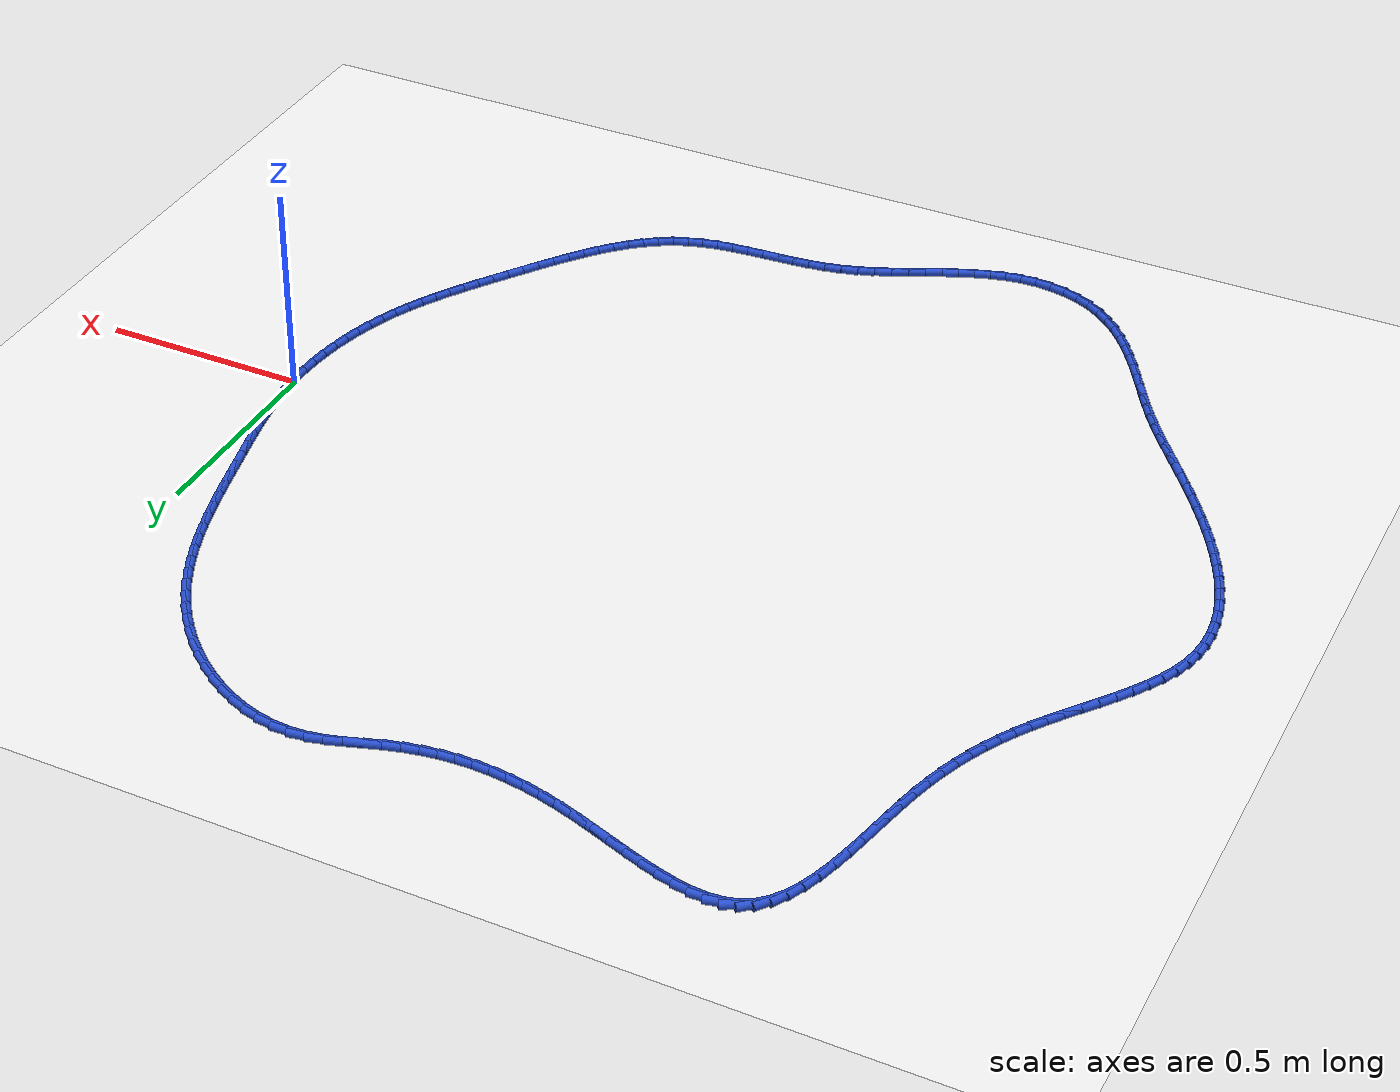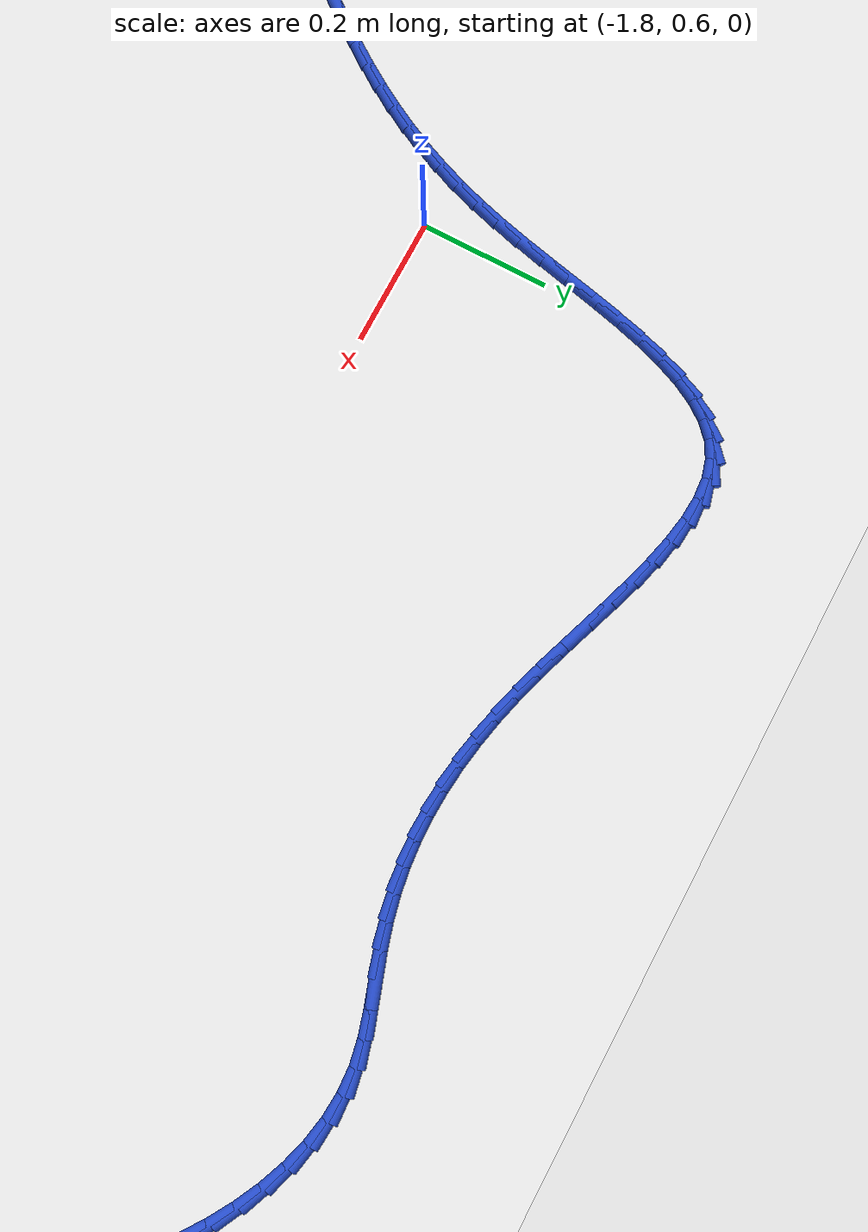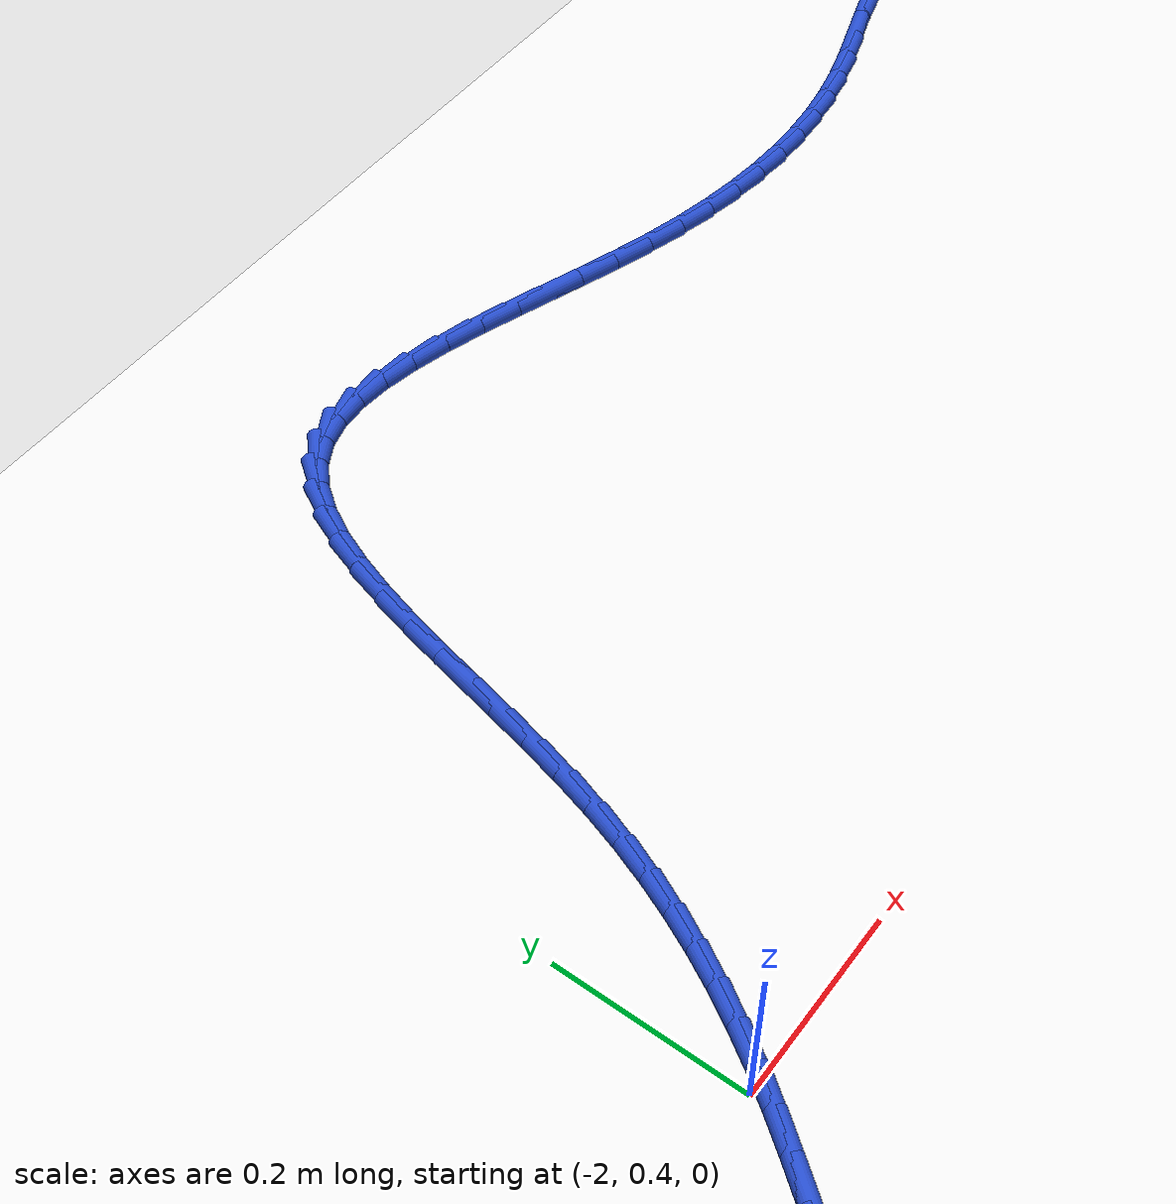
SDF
<sdf version="1.6">
 <world name="default">
  <light name="sun" type="directional">
   <pose>0 0 10 0 -0 0</pose>
   <diffuse>0.8 0.8 0.8 1</diffuse>
   <specular>0.2 0.2 0.2 1</specular>
   <attenuation>
    <range>1000</range>
    <constant>0.9</constant>
    <linear>0.01</linear>
    <quadratic>0.001</quadratic>
   </attenuation>
   <direction>-0.5 0.1 -0.9</direction>
  </light>
  <model name="ground_plane">
   <static>1</static>
   <link name="link">
    <collision name="collision">
     <geometry><plane><normal>0 0 1</normal><size>100 100</size></plane></geometry>
     <surface><friction><ode><mu>100</mu><mu2>50</mu2></ode></friction></surface>
    </collision>
    <visual name="visual">
     <cast_shadows>0</cast_shadows>
     <geometry><plane><normal>0 0 1</normal><size>100 100</size></plane></geometry>
     <material>
      <script><uri>file://media/materials/scripts/gazebo.material</uri><name>Gazebo/WhiteGlow</name></script>
     </material>
    </visual>
   </link>
  </model>
  <gravity>0 0 -9.8</gravity>
  <magnetic_field>6e-06 2.3e-05 -4.2e-05</magnetic_field>
  <atmosphere type="adiabatic"/>
  <physics name="default_physics" default="0" type="ode">
   <max_step_size>0.001</max_step_size>
   <real_time_factor>1</real_time_factor>
   <real_time_update_rate>1000</real_time_update_rate>
  </physics>
  <scene><ambient>0.4 0.4 0.4 1</ambient><background>0.7 0.7 0.7 1</background><shadows>1</shadows></scene>
  <spherical_coordinates>
   <surface_model>EARTH_WGS84</surface_model>
   <latitude_deg>0</latitude_deg>
   <longitude_deg>0</longitude_deg>
   <elevation>0</elevation>
   <heading_deg>0</heading_deg>
  </spherical_coordinates>
  <model name="line">
   <link name="link_0">
    <pose>-1.734723475976807e-17 4.85722573273506e-17 0.01 0 1.57 -1.515405610957278</pose>
    <collision name="collision">
     <geometry><cylinder><radius>0.01</radius><length>0.08</length></cylinder></geometry>
    </collision>
    <visual name="visual">
     <material>
      <script><name>Gazebo/Blue</name><uri>file://media/materials/scripts/gazebo.material</uri></script>
     </material>
     <geometry><cylinder><radius>0.01</radius><length>0.08</length></cylinder></geometry>
    </visual>
   </link>
   <link name="link_1">
    <pose>-0.0021986254997409475 0.039652429999444225 0.01 0 1.57 -1.4713430195479442</pose>
    <collision name="collision">
     <geometry><cylinder><radius>0.01</radius><length>0.08</length></cylinder></geometry>
    </collision>
    <visual name="visual">
     <material>
      <script><name>Gazebo/Blue</name><uri>file://media/materials/scripts/gazebo.material</uri></script>
     </material>
     <geometry><cylinder><radius>0.01</radius><length>0.08</length></cylinder></geometry>
    </visual>
   </link>
   <link name="link_2">
    <pose>-0.006132129484228086 0.07907320767697612 0.01 0 1.57 -1.433098512157439</pose>
    <collision name="collision">
     <geometry><cylinder><radius>0.01</radius><length>0.08</length></cylinder></geometry>
    </collision>
    <visual name="visual">
     <material>
      <script><name>Gazebo/Blue</name><uri>file://media/materials/scripts/gazebo.material</uri></script>
     </material>
     <geometry><cylinder><radius>0.01</radius><length>0.08</length></cylinder></geometry>
    </visual>
   </link>
   <link name="link_3">
    <pose>-0.011568378197984274 0.11830292878780539 0.01 0 1.57 -1.40083018038586</pose>
    <collision name="collision">
     <geometry><cylinder><radius>0.01</radius><length>0.08</length></cylinder></geometry>
    </collision>
    <visual name="visual">
     <material>
      <script><name>Gazebo/Blue</name><uri>file://media/materials/scripts/gazebo.material</uri></script>
     </material>
     <geometry><cylinder><radius>0.01</radius><length>0.08</length></cylinder></geometry>
    </visual>
   </link>
   <link name="link_4">
    <pose>-0.018275237885532362 0.15738218908714177 0.01 0 1.57 -1.3745987916572162</pose>
    <collision name="collision">
     <geometry><cylinder><radius>0.01</radius><length>0.08</length></cylinder></geometry>
    </collision>
    <visual name="visual">
     <material>
      <script><name>Gazebo/Blue</name><uri>file://media/materials/scripts/gazebo.material</uri></script>
     </material>
     <geometry><cylinder><radius>0.01</radius><length>0.08</length></cylinder></geometry>
    </visual>
   </link>
   <link name="link_5">
    <pose>-0.026020574791395194 0.19635158433019478 0.01 0 1.57 -1.3544016644304093</pose>
    <collision name="collision">
     <geometry><cylinder><radius>0.01</radius><length>0.08</length></cylinder></geometry>
    </collision>
    <visual name="visual">
     <material>
      <script><name>Gazebo/Blue</name><uri>file://media/materials/scripts/gazebo.material</uri></script>
     </material>
     <geometry><cylinder><radius>0.01</radius><length>0.08</length></cylinder></geometry>
    </visual>
   </link>
   <link name="link_6">
    <pose>-0.0345722551600956 0.2352517102721742 0.01 0 1.57 -1.3402013848472585</pose>
    <collision name="collision">
     <geometry><cylinder><radius>0.01</radius><length>0.08</length></cylinder></geometry>
    </collision>
    <visual name="visual">
     <material>
      <script><name>Gazebo/Blue</name><uri>file://media/materials/scripts/gazebo.material</uri></script>
     </material>
     <geometry><cylinder><radius>0.01</radius><length>0.08</length></cylinder></geometry>
    </visual>
   </link>
   <link name="link_7">
    <pose>-0.043698145236156435 0.2741231626682896 0.01 0 1.57 -1.3319478990949911</pose>
    <collision name="collision">
     <geometry><cylinder><radius>0.01</radius><length>0.08</length></cylinder></geometry>
    </collision>
    <visual name="visual">
     <material>
      <script><name>Gazebo/Blue</name><uri>file://media/materials/scripts/gazebo.material</uri></script>
     </material>
     <geometry><cylinder><radius>0.01</radius><length>0.08</length></cylinder></geometry>
    </visual>
   </link>
   <link name="link_8">
    <pose>-0.05316611126410055 0.3130065372737507 0.01 0 1.57 -1.3295651523588803</pose>
    <collision name="collision">
     <geometry><cylinder><radius>0.01</radius><length>0.08</length></cylinder></geometry>
    </collision>
    <visual name="visual">
     <material>
      <script><name>Gazebo/Blue</name><uri>file://media/materials/scripts/gazebo.material</uri></script>
     </material>
     <geometry><cylinder><radius>0.01</radius><length>0.08</length></cylinder></geometry>
    </visual>
   </link>
   <link name="link_9">
    <pose>-0.06274511677212218 0.35194210177137425 0.01 0 1.57 -1.3297239635796314</pose>
    <collision name="collision">
     <geometry><cylinder><radius>0.01</radius><length>0.08</length></cylinder></geometry>
    </collision>
    <visual name="visual">
     <material>
      <script><name>Gazebo/Blue</name><uri>file://media/materials/scripts/gazebo.material</uri></script>
     </material>
     <geometry><cylinder><radius>0.01</radius><length>0.08</length></cylinder></geometry>
    </visual>
   </link>
   <link name="link_10">
    <pose>-0.07233097181801215 0.3909321985147546 0.01 0 1.57 -1.3261030435640409</pose>
    <collision name="collision">
     <geometry><cylinder><radius>0.01</radius><length>0.08</length></cylinder></geometry>
    </collision>
    <visual name="visual">
     <material>
      <script><name>Gazebo/Blue</name><uri>file://media/materials/scripts/gazebo.material</uri></script>
     </material>
     <geometry><cylinder><radius>0.01</radius><length>0.08</length></cylinder></geometry>
    </visual>
   </link>
   <link name="link_11">
    <pose>-0.08206271722990452 0.4299064472763352 0.01 0 1.57 -1.317984143536847</pose>
    <collision name="collision">
     <geometry><cylinder><radius>0.01</radius><length>0.08</length></cylinder></geometry>
    </collision>
    <visual name="visual">
     <material>
      <script><name>Gazebo/Blue</name><uri>file://media/materials/scripts/gazebo.material</uri></script>
     </material>
     <geometry><cylinder><radius>0.01</radius><length>0.08</length></cylinder></geometry>
    </visual>
   </link>
   <link name="link_12">
    <pose>-0.09210690837803741 0.4687862413672521 0.01 0 1.57 -1.305342546793271</pose>
    <collision name="collision">
     <geometry><cylinder><radius>0.01</radius><length>0.08</length></cylinder></geometry>
    </collision>
    <visual name="visual">
     <material>
      <script><name>Gazebo/Blue</name><uri>file://media/materials/scripts/gazebo.material</uri></script>
     </material>
     <geometry><cylinder><radius>0.01</radius><length>0.08</length></cylinder></geometry>
    </visual>
   </link>
   <link name="link_13">
    <pose>-0.10263010063264895 0.5074929740986415 0.01 0 1.57 -1.2881364495051462</pose>
    <collision name="collision">
     <geometry><cylinder><radius>0.01</radius><length>0.08</length></cylinder></geometry>
    </collision>
    <visual name="visual">
     <material>
      <script><name>Gazebo/Blue</name><uri>file://media/materials/scripts/gazebo.material</uri></script>
     </material>
     <geometry><cylinder><radius>0.01</radius><length>0.08</length></cylinder></geometry>
    </visual>
   </link>
   <link name="link_14">
    <pose>-0.1137988493639773 0.5459480387816392 0.01 0 1.57 -1.2663144781094937</pose>
    <collision name="collision">
     <geometry><cylinder><radius>0.01</radius><length>0.08</length></cylinder></geometry>
    </collision>
    <visual name="visual">
     <material>
      <script><name>Gazebo/Blue</name><uri>file://media/materials/scripts/gazebo.material</uri></script>
     </material>
     <geometry><cylinder><radius>0.01</radius><length>0.08</length></cylinder></geometry>
    </visual>
   </link>
   <link name="link_15">
    <pose>-0.1257797099422605 0.5840728287273813 0.01 0 1.57 -1.239826303305257</pose>
    <collision name="collision">
     <geometry><cylinder><radius>0.01</radius><length>0.08</length></cylinder></geometry>
    </collision>
    <visual name="visual">
     <material>
      <script><name>Gazebo/Blue</name><uri>file://media/materials/scripts/gazebo.material</uri></script>
     </material>
     <geometry><cylinder><radius>0.01</radius><length>0.08</length></cylinder></geometry>
    </visual>
   </link>
   <link name="link_16">
    <pose>-0.13873923773773672 0.6217887372470041 0.01 0 1.57 -1.2086366638595052</pose>
    <collision name="collision">
     <geometry><cylinder><radius>0.01</radius><length>0.08</length></cylinder></geometry>
    </collision>
    <visual name="visual">
     <material>
      <script><name>Gazebo/Blue</name><uri>file://media/materials/scripts/gazebo.material</uri></script>
     </material>
     <geometry><cylinder><radius>0.01</radius><length>0.08</length></cylinder></geometry>
    </visual>
   </link>
   <link name="link_17">
    <pose>-0.15284398812064406 0.6590171576516434 0.01 0 1.57 -1.1727429122406923</pose>
    <collision name="collision">
     <geometry><cylinder><radius>0.01</radius><length>0.08</length></cylinder></geometry>
    </collision>
    <visual name="visual">
     <material>
      <script><name>Gazebo/Blue</name><uri>file://media/materials/scripts/gazebo.material</uri></script>
     </material>
     <geometry><cylinder><radius>0.01</radius><length>0.08</length></cylinder></geometry>
    </visual>
   </link>
   <link name="link_18">
    <pose>-0.16826051646122073 0.6956794832524353 0.01 0 1.57 -1.1321957447311972</pose>
    <collision name="collision">
     <geometry><cylinder><radius>0.01</radius><length>0.08</length></cylinder></geometry>
    </collision>
    <visual name="visual">
     <material>
      <script><name>Gazebo/Blue</name><uri>file://media/materials/scripts/gazebo.material</uri></script>
     </material>
     <geometry><cylinder><radius>0.01</radius><length>0.08</length></cylinder></geometry>
    </visual>
   </link>
   <link name="link_19">
    <pose>-0.18515537812970465 0.7316971073605157 0.01 0 1.57 -1.0871220316178278</pose>
    <collision name="collision">
     <geometry><cylinder><radius>0.01</radius><length>0.08</length></cylinder></geometry>
    </collision>
    <visual name="visual">
     <material>
      <script><name>Gazebo/Blue</name><uri>file://media/materials/scripts/gazebo.material</uri></script>
     </material>
     <geometry><cylinder><radius>0.01</radius><length>0.08</length></cylinder></geometry>
    </visual>
   </link>
   <link name="link_20">
    <pose>-0.20369512849633414 0.7669914232870211 0.01 0 1.57 -1.0377476398930954</pose>
    <collision name="collision">
     <geometry><cylinder><radius>0.01</radius><length>0.08</length></cylinder></geometry>
    </collision>
    <visual name="visual">
     <material>
      <script><name>Gazebo/Blue</name><uri>file://media/materials/scripts/gazebo.material</uri></script>
     </material>
     <geometry><cylinder><radius>0.01</radius><length>0.08</length></cylinder></geometry>
    </visual>
   </link>
   <link name="link_21">
    <pose>-0.22404632293134738 0.8014838243430876 0.01 0 1.57 -0.9844170006511085</pose>
    <collision name="collision">
     <geometry><cylinder><radius>0.01</radius><length>0.08</length></cylinder></geometry>
    </collision>
    <visual name="visual">
     <material>
      <script><name>Gazebo/Blue</name><uri>file://media/materials/scripts/gazebo.material</uri></script>
     </material>
     <geometry><cylinder><radius>0.01</radius><length>0.08</length></cylinder></geometry>
    </visual>
   </link>
   <link name="link_22">
    <pose>-0.2463755168049822 0.8350957038398504 0.01 0 1.57 -0.9276052621905037</pose>
    <collision name="collision">
     <geometry><cylinder><radius>0.01</radius><length>0.08</length></cylinder></geometry>
    </collision>
    <visual name="visual">
     <material>
      <script><name>Gazebo/Blue</name><uri>file://media/materials/scripts/gazebo.material</uri></script>
     </material>
     <geometry><cylinder><radius>0.01</radius><length>0.08</length></cylinder></geometry>
    </visual>
   </link>
   <link name="link_23">
    <pose>-0.27084926548747706 0.8677484550884466 0.01 0 1.57 -0.8679203692435556</pose>
    <collision name="collision">
     <geometry><cylinder><radius>0.01</radius><length>0.08</length></cylinder></geometry>
    </collision>
    <visual name="visual">
     <material>
      <script><name>Gazebo/Blue</name><uri>file://media/materials/scripts/gazebo.material</uri></script>
     </material>
     <geometry><cylinder><radius>0.01</radius><length>0.08</length></cylinder></geometry>
    </visual>
   </link>
   <link name="link_24">
    <pose>-0.29763389407191215 0.8993633070807878 0.01 0 1.57 -0.8066614649383962</pose>
    <collision name="collision">
     <geometry><cylinder><radius>0.01</radius><length>0.08</length></cylinder></geometry>
    </collision>
    <visual name="visual">
     <material>
      <script><name>Gazebo/Blue</name><uri>file://media/materials/scripts/gazebo.material</uri></script>
     </material>
     <geometry><cylinder><radius>0.01</radius><length>0.08</length></cylinder></geometry>
    </visual>
   </link>
   <link name="link_25">
    <pose>-0.3267887539432026 0.9297851554162345 0.01 0 1.57 -0.7450201444126946</pose>
    <collision name="collision">
     <geometry><cylinder><radius>0.01</radius><length>0.08</length></cylinder></geometry>
    </collision>
    <visual name="visual">
     <material>
      <script><name>Gazebo/Blue</name><uri>file://media/materials/scripts/gazebo.material</uri></script>
     </material>
     <geometry><cylinder><radius>0.01</radius><length>0.08</length></cylinder></geometry>
    </visual>
   </link>
   <link name="link_26">
    <pose>-0.35809643312897166 0.9586614052419729 0.01 0 1.57 -0.681815909023707</pose>
    <collision name="collision">
     <geometry><cylinder><radius>0.01</radius><length>0.08</length></cylinder></geometry>
    </collision>
    <visual name="visual">
     <material>
      <script><name>Gazebo/Blue</name><uri>file://media/materials/scripts/gazebo.material</uri></script>
     </material>
     <geometry><cylinder><radius>0.01</radius><length>0.08</length></cylinder></geometry>
    </visual>
   </link>
   <link name="link_27">
    <pose>-0.39129535376694086 0.98560794618358 0.01 0 1.57 -0.6155791142099029</pose>
    <collision name="collision">
     <geometry><cylinder><radius>0.01</radius><length>0.08</length></cylinder></geometry>
    </collision>
    <visual name="visual">
     <material>
      <script><name>Gazebo/Blue</name><uri>file://media/materials/scripts/gazebo.material</uri></script>
     </material>
     <geometry><cylinder><radius>0.01</radius><length>0.08</length></cylinder></geometry>
    </visual>
   </link>
   <link name="link_28">
    <pose>-0.4261239379948326 1.0102406678666345 0.01 0 1.57 -0.5448117098480703</pose>
    <collision name="collision">
     <geometry><cylinder><radius>0.01</radius><length>0.08</length></cylinder></geometry>
    </collision>
    <visual name="visual">
     <material>
      <script><name>Gazebo/Blue</name><uri>file://media/materials/scripts/gazebo.material</uri></script>
     </material>
     <geometry><cylinder><radius>0.01</radius><length>0.08</length></cylinder></geometry>
    </visual>
   </link>
   <link name="link_29">
    <pose>-0.4623206079503682 1.032175459916712 0.01 0 1.57 -0.4679524198341195</pose>
    <collision name="collision">
     <geometry><cylinder><radius>0.01</radius><length>0.08</length></cylinder></geometry>
    </collision>
    <visual name="visual">
     <material>
      <script><name>Gazebo/Blue</name><uri>file://media/materials/scripts/gazebo.material</uri></script>
     </material>
     <geometry><cylinder><radius>0.01</radius><length>0.08</length></cylinder></geometry>
    </visual>
   </link>
   <link name="link_30">
    <pose>-0.4996237857712698 1.0510282119593914 0.01 0 1.57 -0.38338110124971014</pose>
    <collision name="collision">
     <geometry><cylinder><radius>0.01</radius><length>0.08</length></cylinder></geometry>
    </collision>
    <visual name="visual">
     <material>
      <script><name>Gazebo/Blue</name><uri>file://media/materials/scripts/gazebo.material</uri></script>
     </material>
     <geometry><cylinder><radius>0.01</radius><length>0.08</length></cylinder></geometry>
    </visual>
   </link>
   <link name="link_31">
    <pose>-0.5377718935952589 1.0664148136202494 0.01 0 1.57 -0.2894873153356461</pose>
    <collision name="collision">
     <geometry><cylinder><radius>0.01</radius><length>0.08</length></cylinder></geometry>
    </collision>
    <visual name="visual">
     <material>
      <script><name>Gazebo/Blue</name><uri>file://media/materials/scripts/gazebo.material</uri></script>
     </material>
     <geometry><cylinder><radius>0.01</radius><length>0.08</length></cylinder></geometry>
    </visual>
   </link>
   <link name="link_32">
    <pose>-0.5765033535600577 1.0779511545248635 0.01 0 1.57 -0.18484051677864688</pose>
    <collision name="collision">
     <geometry><cylinder><radius>0.01</radius><length>0.08</length></cylinder></geometry>
    </collision>
    <visual name="visual">
     <material>
      <script><name>Gazebo/Blue</name><uri>file://media/materials/scripts/gazebo.material</uri></script>
     </material>
     <geometry><cylinder><radius>0.01</radius><length>0.08</length></cylinder></geometry>
    </visual>
   </link>
   <link name="link_33">
    <pose>-0.6155565878033881 1.0852531242988117 0.01 0 1.57 -0.06850050351292601</pose>
    <collision name="collision">
     <geometry><cylinder><radius>0.01</radius><length>0.08</length></cylinder></geometry>
    </collision>
    <visual name="visual">
     <material>
      <script><name>Gazebo/Blue</name><uri>file://media/materials/scripts/gazebo.material</uri></script>
     </material>
     <geometry><cylinder><radius>0.01</radius><length>0.08</length></cylinder></geometry>
    </visual>
   </link>
   <link name="link_34">
    <pose>-0.6546700184629712 1.0879366125676708 0.01 0 1.57 0.059528184232837594</pose>
    <collision name="collision">
     <geometry><cylinder><radius>0.01</radius><length>0.08</length></cylinder></geometry>
    </collision>
    <visual name="visual">
     <material>
      <script><name>Gazebo/Blue</name><uri>file://media/materials/scripts/gazebo.material</uri></script>
     </material>
     <geometry><cylinder><radius>0.01</radius><length>0.08</length></cylinder></geometry>
    </visual>
   </link>
   <link name="link_35">
    <pose>-0.6935820676765297 1.0856175089570184 0.01 0 1.57 0.19024913804069496</pose>
    <collision name="collision">
     <geometry><cylinder><radius>0.01</radius><length>0.08</length></cylinder></geometry>
    </collision>
    <visual name="visual">
     <material>
      <script><name>Gazebo/Blue</name><uri>file://media/materials/scripts/gazebo.material</uri></script>
     </material>
     <geometry><cylinder><radius>0.01</radius><length>0.08</length></cylinder></geometry>
    </visual>
   </link>
   <link name="link_36">
    <pose>-0.7320831098524112 1.0782030474477207 0.01 0 1.57 0.28374969977899694</pose>
    <collision name="collision">
     <geometry><cylinder><radius>0.01</radius><length>0.08</length></cylinder></geometry>
    </collision>
    <visual name="visual">
     <material>
      <script><name>Gazebo/Blue</name><uri>file://media/materials/scripts/gazebo.material</uri></script>
     </material>
     <geometry><cylinder><radius>0.01</radius><length>0.08</length></cylinder></geometry>
    </visual>
   </link>
   <link name="link_37">
    <pose>-0.7702272615674245 1.0670795079046156 0.01 0 1.57 0.32971492184797635</pose>
    <collision name="collision">
     <geometry><cylinder><radius>0.01</radius><length>0.08</length></cylinder></geometry>
    </collision>
    <visual name="visual">
     <material>
      <script><name>Gazebo/Blue</name><uri>file://media/materials/scripts/gazebo.material</uri></script>
     </material>
     <geometry><cylinder><radius>0.01</radius><length>0.08</length></cylinder></geometry>
    </visual>
   </link>
   <link name="link_38">
    <pose>-0.8081521295117319 1.0541013763547509 0.01 0 1.57 0.3303737932049245</pose>
    <collision name="collision">
     <geometry><cylinder><radius>0.01</radius><length>0.08</length></cylinder></geometry>
    </collision>
    <visual name="visual">
     <material>
      <script><name>Gazebo/Blue</name><uri>file://media/materials/scripts/gazebo.material</uri></script>
     </material>
     <geometry><cylinder><radius>0.01</radius><length>0.08</length></cylinder></geometry>
    </visual>
   </link>
   <link name="link_39">
    <pose>-0.8459953533858356 1.0411233239446331 0.01 0 1.57 0.28673895481645933</pose>
    <collision name="collision">
     <geometry><cylinder><radius>0.01</radius><length>0.08</length></cylinder></geometry>
    </collision>
    <visual name="visual">
     <material>
      <script><name>Gazebo/Blue</name><uri>file://media/materials/scripts/gazebo.material</uri></script>
     </material>
     <geometry><cylinder><radius>0.01</radius><length>0.08</length></cylinder></geometry>
    </visual>
   </link>
   <link name="link_40">
    <pose>-0.8838929302774444 1.0299486630898318 0.01 0 1.57 0.22062755832793557</pose>
    <collision name="collision">
     <geometry><cylinder><radius>0.01</radius><length>0.08</length></cylinder></geometry>
    </collision>
    <visual name="visual">
     <material>
      <script><name>Gazebo/Blue</name><uri>file://media/materials/scripts/gazebo.material</uri></script>
     </material>
     <geometry><cylinder><radius>0.01</radius><length>0.08</length></cylinder></geometry>
    </visual>
   </link>
   <link name="link_41">
    <pose>-0.9219499166320745 1.021413301030985 0.01 0 1.57 0.15342667424321121</pose>
    <collision name="collision">
     <geometry><cylinder><radius>0.01</radius><length>0.08</length></cylinder></geometry>
    </collision>
    <visual name="visual">
     <material>
      <script><name>Gazebo/Blue</name><uri>file://media/materials/scripts/gazebo.material</uri></script>
     </material>
     <geometry><cylinder><radius>0.01</radius><length>0.08</length></cylinder></geometry>
    </visual>
   </link>
   <link name="link_42">
    <pose>-0.9602438094218115 1.015491457101588 0.01 0 1.57 0.08692017934584999</pose>
    <collision name="collision">
     <geometry><cylinder><radius>0.01</radius><length>0.08</length></cylinder></geometry>
    </collision>
    <visual name="visual">
     <material>
      <script><name>Gazebo/Blue</name><uri>file://media/materials/scripts/gazebo.material</uri></script>
     </material>
     <geometry><cylinder><radius>0.01</radius><length>0.08</length></cylinder></geometry>
    </visual>
   </link>
   <link name="link_43">
    <pose>-0.9988511420798942 1.0121272241606731 0.01 0 1.57 0.022114052915809125</pose>
    <collision name="collision">
     <geometry><cylinder><radius>0.01</radius><length>0.08</length></cylinder></geometry>
    </collision>
    <visual name="visual">
     <material>
      <script><name>Gazebo/Blue</name><uri>file://media/materials/scripts/gazebo.material</uri></script>
     </material>
     <geometry><cylinder><radius>0.01</radius><length>0.08</length></cylinder></geometry>
    </visual>
   </link>
   <link name="link_44">
    <pose>-1.0378484480395604 1.0112646950672712 0.01 0 1.57 -0.04009797490723226</pose>
    <collision name="collision">
     <geometry><cylinder><radius>0.01</radius><length>0.08</length></cylinder></geometry>
    </collision>
    <visual name="visual">
     <material>
      <script><name>Gazebo/Blue</name><uri>file://media/materials/scripts/gazebo.material</uri></script>
     </material>
     <geometry><cylinder><radius>0.01</radius><length>0.08</length></cylinder></geometry>
    </visual>
   </link>
   <link name="link_45">
    <pose>-1.0773122607340488 1.0128479626804148 0.01 0 1.57 -0.09898733409651839</pose>
    <collision name="collision">
     <geometry><cylinder><radius>0.01</radius><length>0.08</length></cylinder></geometry>
    </collision>
    <visual name="visual">
     <material>
      <script><name>Gazebo/Blue</name><uri>file://media/materials/scripts/gazebo.material</uri></script>
     </material>
     <geometry><cylinder><radius>0.01</radius><length>0.08</length></cylinder></geometry>
    </visual>
   </link>
   <link name="link_46">
    <pose>-1.1173191135965985 1.0168211198591361 0.01 0 1.57 -0.1540177070334375</pose>
    <collision name="collision">
     <geometry><cylinder><radius>0.01</radius><length>0.08</length></cylinder></geometry>
    </collision>
    <visual name="visual">
     <material>
      <script><name>Gazebo/Blue</name><uri>file://media/materials/scripts/gazebo.material</uri></script>
     </material>
     <geometry><cylinder><radius>0.01</radius><length>0.08</length></cylinder></geometry>
    </visual>
   </link>
   <link name="link_47">
    <pose>-1.1579455400604468 1.023128259462466 0.01 0 1.57 -0.20484689366956407</pose>
    <collision name="collision">
     <geometry><cylinder><radius>0.01</radius><length>0.08</length></cylinder></geometry>
    </collision>
    <visual name="visual">
     <material>
      <script><name>Gazebo/Blue</name><uri>file://media/materials/scripts/gazebo.material</uri></script>
     </material>
     <geometry><cylinder><radius>0.01</radius><length>0.08</length></cylinder></geometry>
    </visual>
   </link>
   <link name="link_48">
    <pose>-1.1992680735588324 1.0317134743494374 0.01 0 1.57 -0.25130912331340033</pose>
    <collision name="collision">
     <geometry><cylinder><radius>0.01</radius><length>0.08</length></cylinder></geometry>
    </collision>
    <visual name="visual">
     <material>
      <script><name>Gazebo/Blue</name><uri>file://media/materials/scripts/gazebo.material</uri></script>
     </material>
     <geometry><cylinder><radius>0.01</radius><length>0.08</length></cylinder></geometry>
    </visual>
   </link>
   <link name="link_49">
    <pose>-1.241363247524994 1.0425208573790812 0.01 0 1.57 -0.2925340425971711</pose>
    <collision name="collision">
     <geometry><cylinder><radius>0.01</radius><length>0.08</length></cylinder></geometry>
    </collision>
    <visual name="visual">
     <material>
      <script><name>Gazebo/Blue</name><uri>file://media/materials/scripts/gazebo.material</uri></script>
     </material>
     <geometry><cylinder><radius>0.01</radius><length>0.08</length></cylinder></geometry>
    </visual>
   </link>
   <link name="link_50">
    <pose>-1.2842753483489588 1.0554448913430603 0.01 0 1.57 -0.32141922913595883</pose>
    <collision name="collision">
     <geometry><cylinder><radius>0.01</radius><length>0.08</length></cylinder></geometry>
    </collision>
    <visual name="visual">
     <material>
      <script><name>Gazebo/Blue</name><uri>file://media/materials/scripts/gazebo.material</uri></script>
     </material>
     <geometry><cylinder><radius>0.01</radius><length>0.08</length></cylinder></geometry>
    </visual>
   </link>
   <link name="link_51">
    <pose>-1.327749878417648 1.0699203984549739 0.01 0 1.57 -0.3355626292041894</pose>
    <collision name="collision">
     <geometry><cylinder><radius>0.01</radius><length>0.08</length></cylinder></geometry>
    </collision>
    <visual name="visual">
     <material>
      <script><name>Gazebo/Blue</name><uri>file://media/materials/scripts/gazebo.material</uri></script>
     </material>
     <geometry><cylinder><radius>0.01</radius><length>0.08</length></cylinder></geometry>
    </visual>
   </link>
   <link name="link_52">
    <pose>-1.3713704661629464 1.0851331679314349 0.01 0 1.57 -0.3358798256639726</pose>
    <collision name="collision">
     <geometry><cylinder><radius>0.01</radius><length>0.08</length></cylinder></geometry>
    </collision>
    <visual name="visual">
     <material>
      <script><name>Gazebo/Blue</name><uri>file://media/materials/scripts/gazebo.material</uri></script>
     </material>
     <geometry><cylinder><radius>0.01</radius><length>0.08</length></cylinder></geometry>
    </visual>
   </link>
   <link name="link_53">
    <pose>-1.4147191429887989 1.1002665320610492 0.01 0 1.57 -0.32212376673585585</pose>
    <collision name="collision">
     <geometry><cylinder><radius>0.01</radius><length>0.08</length></cylinder></geometry>
    </collision>
    <visual name="visual">
     <material>
      <script><name>Gazebo/Blue</name><uri>file://media/materials/scripts/gazebo.material</uri></script>
     </material>
     <geometry><cylinder><radius>0.01</radius><length>0.08</length></cylinder></geometry>
    </visual>
   </link>
   <link name="link_54">
    <pose>-1.4573779402991522 1.1145038231324222 0.01 0 1.57 -0.29276484376699224</pose>
    <collision name="collision">
     <geometry><cylinder><radius>0.01</radius><length>0.08</length></cylinder></geometry>
    </collision>
    <visual name="visual">
     <material>
      <script><name>Gazebo/Blue</name><uri>file://media/materials/scripts/gazebo.material</uri></script>
     </material>
     <geometry><cylinder><radius>0.01</radius><length>0.08</length></cylinder></geometry>
    </visual>
   </link>
   <link name="link_55">
    <pose>-1.4989288894979538 1.1270283734341613 0.01 0 1.57 -0.24471666229600572</pose>
    <collision name="collision">
     <geometry><cylinder><radius>0.01</radius><length>0.08</length></cylinder></geometry>
    </collision>
    <visual name="visual">
     <material>
      <script><name>Gazebo/Blue</name><uri>file://media/materials/scripts/gazebo.material</uri></script>
     </material>
     <geometry><cylinder><radius>0.01</radius><length>0.08</length></cylinder></geometry>
    </visual>
   </link>
   <link name="link_56">
    <pose>-1.5389540219891487 1.1370235152548718 0.01 0 1.57 -0.1728591164609394</pose>
    <collision name="collision">
     <geometry><cylinder><radius>0.01</radius><length>0.08</length></cylinder></geometry>
    </collision>
    <visual name="visual">
     <material>
      <script><name>Gazebo/Blue</name><uri>file://media/materials/scripts/gazebo.material</uri></script>
     </material>
     <geometry><cylinder><radius>0.01</radius><length>0.08</length></cylinder></geometry>
    </visual>
   </link>
   <link name="link_57">
    <pose>-1.5770353691766839 1.1436725808831603 0.01 0 1.57 -0.06949457277430804</pose>
    <collision name="collision">
     <geometry><cylinder><radius>0.01</radius><length>0.08</length></cylinder></geometry>
    </collision>
    <visual name="visual">
     <material>
      <script><name>Gazebo/Blue</name><uri>file://media/materials/scripts/gazebo.material</uri></script>
     </material>
     <geometry><cylinder><radius>0.01</radius><length>0.08</length></cylinder></geometry>
    </visual>
   </link>
   <link name="link_58">
    <pose>-1.6127549624645054 1.1461589026076324 0.01 0 1.57 0.07554206096373504</pose>
    <collision name="collision">
     <geometry><cylinder><radius>0.01</radius><length>0.08</length></cylinder></geometry>
    </collision>
    <visual name="visual">
     <material>
      <script><name>Gazebo/Blue</name><uri>file://media/materials/scripts/gazebo.material</uri></script>
     </material>
     <geometry><cylinder><radius>0.01</radius><length>0.08</length></cylinder></geometry>
    </visual>
   </link>
   <link name="link_59">
    <pose>-1.6456948332565593 1.1436658127168946 0.01 0 1.57 0.27180354752542457</pose>
    <collision name="collision">
     <geometry><cylinder><radius>0.01</radius><length>0.08</length></cylinder></geometry>
    </collision>
    <visual name="visual">
     <material>
      <script><name>Gazebo/Blue</name><uri>file://media/materials/scripts/gazebo.material</uri></script>
     </material>
     <geometry><cylinder><radius>0.01</radius><length>0.08</length></cylinder></geometry>
    </visual>
   </link>
   <link name="link_60">
    <pose>-1.6754370129567935 1.1353766434995536 0.01 0 1.57 0.515961949990352</pose>
    <collision name="collision">
     <geometry><cylinder><radius>0.01</radius><length>0.08</length></cylinder></geometry>
    </collision>
    <visual name="visual">
     <material>
      <script><name>Gazebo/Blue</name><uri>file://media/materials/scripts/gazebo.material</uri></script>
     </material>
     <geometry><cylinder><radius>0.01</radius><length>0.08</length></cylinder></geometry>
    </visual>
   </link>
   <link name="link_61">
    <pose>-1.7015971448208291 1.1205382939595308 0.01 0 1.57 0.7538740013303692</pose>
    <collision name="collision">
     <geometry><cylinder><radius>0.01</radius><length>0.08</length></cylinder></geometry>
    </collision>
    <visual name="visual">
     <material>
      <script><name>Gazebo/Blue</name><uri>file://media/materials/scripts/gazebo.material</uri></script>
     </material>
     <geometry><cylinder><radius>0.01</radius><length>0.08</length></cylinder></geometry>
    </visual>
   </link>
   <link name="link_62">
    <pose>-1.7242515883038851 1.0992689693228221 0.01 0 1.57 0.9429869830477323</pose>
    <collision name="collision">
     <geometry><cylinder><radius>0.01</radius><length>0.08</length></cylinder></geometry>
    </collision>
    <visual name="visual">
     <material>
      <script><name>Gazebo/Blue</name><uri>file://media/materials/scripts/gazebo.material</uri></script>
     </material>
     <geometry><cylinder><radius>0.01</radius><length>0.08</length></cylinder></geometry>
    </visual>
   </link>
   <link name="link_63">
    <pose>-1.7438109401475401 1.072318984186676 0.01 0 1.57 1.083602102859504</pose>
    <collision name="collision">
     <geometry><cylinder><radius>0.01</radius><length>0.08</length></cylinder></geometry>
    </collision>
    <visual name="visual">
     <material>
      <script><name>Gazebo/Blue</name><uri>file://media/materials/scripts/gazebo.material</uri></script>
     </material>
     <geometry><cylinder><radius>0.01</radius><length>0.08</length></cylinder></geometry>
    </visual>
   </link>
   <link name="link_64">
    <pose>-1.7606932936030006 1.0404528305432124 0.01 0 1.57 1.1851232731153538</pose>
    <collision name="collision">
     <geometry><cylinder><radius>0.01</radius><length>0.08</length></cylinder></geometry>
    </collision>
    <visual name="visual">
     <material>
      <script><name>Gazebo/Blue</name><uri>file://media/materials/scripts/gazebo.material</uri></script>
     </material>
     <geometry><cylinder><radius>0.01</radius><length>0.08</length></cylinder></geometry>
    </visual>
   </link>
   <link name="link_65">
    <pose>-1.775316741921475 1.0044350003845504 0.01 0 1.57 1.2571152468708502</pose>
    <collision name="collision">
     <geometry><cylinder><radius>0.01</radius><length>0.08</length></cylinder></geometry>
    </collision>
    <visual name="visual">
     <material>
      <script><name>Gazebo/Blue</name><uri>file://media/materials/scripts/gazebo.material</uri></script>
     </material>
     <geometry><cylinder><radius>0.01</radius><length>0.08</length></cylinder></geometry>
    </visual>
   </link>
   <link name="link_66">
    <pose>-1.7880993783541699 0.9650299857028083 0.01 0 1.57 1.3068086994045838</pose>
    <collision name="collision">
     <geometry><cylinder><radius>0.01</radius><length>0.08</length></cylinder></geometry>
    </collision>
    <visual name="visual">
     <material>
      <script><name>Gazebo/Blue</name><uri>file://media/materials/scripts/gazebo.material</uri></script>
     </material>
     <geometry><cylinder><radius>0.01</radius><length>0.08</length></cylinder></geometry>
    </visual>
   </link>
   <link name="link_67">
    <pose>-1.7994592961522937 0.9230022784901067 0.01 0 1.57 1.3390753718841701</pose>
    <collision name="collision">
     <geometry><cylinder><radius>0.01</radius><length>0.08</length></cylinder></geometry>
    </collision>
    <visual name="visual">
     <material>
      <script><name>Gazebo/Blue</name><uri>file://media/materials/scripts/gazebo.material</uri></script>
     </material>
     <geometry><cylinder><radius>0.01</radius><length>0.08</length></cylinder></geometry>
    </visual>
   </link>
   <link name="link_68">
    <pose>-1.8098145885670545 0.8791163707385647 0.01 0 1.57 1.3569355693815515</pose>
    <collision name="collision">
     <geometry><cylinder><radius>0.01</radius><length>0.08</length></cylinder></geometry>
    </collision>
    <visual name="visual">
     <material>
      <script><name>Gazebo/Blue</name><uri>file://media/materials/scripts/gazebo.material</uri></script>
     </material>
     <geometry><cylinder><radius>0.01</radius><length>0.08</length></cylinder></geometry>
    </visual>
   </link>
   <link name="link_69">
    <pose>-1.819583348849659 0.8341367544403004 0.01 0 1.57 1.3619981824513048</pose>
    <collision name="collision">
     <geometry><cylinder><radius>0.01</radius><length>0.08</length></cylinder></geometry>
    </collision>
    <visual name="visual">
     <material>
      <script><name>Gazebo/Blue</name><uri>file://media/materials/scripts/gazebo.material</uri></script>
     </material>
     <geometry><cylinder><radius>0.01</radius><length>0.08</length></cylinder></geometry>
    </visual>
   </link>
   <link name="link_70">
    <pose>-1.8291836702513156 0.7888279215874344 0.01 0 1.57 1.35471810084058</pose>
    <collision name="collision">
     <geometry><cylinder><radius>0.01</radius><length>0.08</length></cylinder></geometry>
    </collision>
    <visual name="visual">
     <material>
      <script><name>Gazebo/Blue</name><uri>file://media/materials/scripts/gazebo.material</uri></script>
     </material>
     <geometry><cylinder><radius>0.01</radius><length>0.08</length></cylinder></geometry>
    </visual>
   </link>
   <link name="link_71">
    <pose>-1.8390336460232308 0.7439543641720847 0.01 0 1.57 1.3344717938092594</pose>
    <collision name="collision">
     <geometry><cylinder><radius>0.01</radius><length>0.08</length></cylinder></geometry>
    </collision>
    <visual name="visual">
     <material>
      <script><name>Gazebo/Blue</name><uri>file://media/materials/scripts/gazebo.material</uri></script>
     </material>
     <geometry><cylinder><radius>0.01</radius><length>0.08</length></cylinder></geometry>
    </visual>
   </link>
   <link name="link_72">
    <pose>-1.8495513694166137 0.700280574186372 0.01 0 1.57 1.3003523546444689</pose>
    <collision name="collision">
     <geometry><cylinder><radius>0.01</radius><length>0.08</length></cylinder></geometry>
    </collision>
    <visual name="visual">
     <material>
      <script><name>Gazebo/Blue</name><uri>file://media/materials/scripts/gazebo.material</uri></script>
     </material>
     <geometry><cylinder><radius>0.01</radius><length>0.08</length></cylinder></geometry>
    </visual>
   </link>
   <link name="link_73">
    <pose>-1.861131903212898 0.6585092076422082 0.01 0 1.57 1.259106848956085</pose>
    <collision name="collision">
     <geometry><cylinder><radius>0.01</radius><length>0.08</length></cylinder></geometry>
    </collision>
    <visual name="visual">
     <material>
      <script><name>Gazebo/Blue</name><uri>file://media/materials/scripts/gazebo.material</uri></script>
     </material>
     <geometry><cylinder><radius>0.01</radius><length>0.08</length></cylinder></geometry>
    </visual>
   </link>
   <link name="link_74">
    <pose>-1.873945456661369 0.6187391969322819 0.01 0 1.57 1.215819242705524</pose>
    <collision name="collision">
     <geometry><cylinder><radius>0.01</radius><length>0.08</length></cylinder></geometry>
    </collision>
    <visual name="visual">
     <material>
      <script><name>Gazebo/Blue</name><uri>file://media/materials/scripts/gazebo.material</uri></script>
     </material>
     <geometry><cylinder><radius>0.01</radius><length>0.08</length></cylinder></geometry>
    </visual>
   </link>
   <link name="link_75">
    <pose>-1.8880352356246086 0.5807284749393391 0.01 0 1.57 1.1713324374699692</pose>
    <collision name="collision">
     <geometry><cylinder><radius>0.01</radius><length>0.08</length></cylinder></geometry>
    </collision>
    <visual name="visual">
     <material>
      <script><name>Gazebo/Blue</name><uri>file://media/materials/scripts/gazebo.material</uri></script>
     </material>
     <geometry><cylinder><radius>0.01</radius><length>0.08</length></cylinder></geometry>
    </visual>
   </link>
   <link name="link_76">
    <pose>-1.9034430105590137 0.5442311205323154 0.01 0 1.57 1.1265762466182048</pose>
    <collision name="collision">
     <geometry><cylinder><radius>0.01</radius><length>0.08</length></cylinder></geometry>
    </collision>
    <visual name="visual">
     <material>
      <script><name>Gazebo/Blue</name><uri>file://media/materials/scripts/gazebo.material</uri></script>
     </material>
     <geometry><cylinder><radius>0.01</radius><length>0.08</length></cylinder></geometry>
    </visual>
   </link>
   <link name="link_77">
    <pose>-1.9202105519209811 0.5090012125801455 0.01 0 1.57 1.0825564240523091</pose>
    <collision name="collision">
     <geometry><cylinder><radius>0.01</radius><length>0.08</length></cylinder></geometry>
    </collision>
    <visual name="visual">
     <material>
      <script><name>Gazebo/Blue</name><uri>file://media/materials/scripts/gazebo.material</uri></script>
     </material>
     <geometry><cylinder><radius>0.01</radius><length>0.08</length></cylinder></geometry>
    </visual>
   </link>
   <link name="link_78">
    <pose>-1.9383796301669056 0.4747928299517657 0.01 0 1.57 1.0402720654731736</pose>
    <collision name="collision">
     <geometry><cylinder><radius>0.01</radius><length>0.08</length></cylinder></geometry>
    </collision>
    <visual name="visual">
     <material>
      <script><name>Gazebo/Blue</name><uri>file://media/materials/scripts/gazebo.material</uri></script>
     </material>
     <geometry><cylinder><radius>0.01</radius><length>0.08</length></cylinder></geometry>
    </visual>
   </link>
   <link name="link_79">
    <pose>-1.9579920157531838 0.44136005151611074 0.01 0 1.57 1.000632323656434</pose>
    <collision name="collision">
     <geometry><cylinder><radius>0.01</radius><length>0.08</length></cylinder></geometry>
    </collision>
    <visual name="visual">
     <material>
      <script><name>Gazebo/Blue</name><uri>file://media/materials/scripts/gazebo.material</uri></script>
     </material>
     <geometry><cylinder><radius>0.01</radius><length>0.08</length></cylinder></geometry>
    </visual>
   </link>
   <link name="link_80">
    <pose>-1.979089479136213 0.40845695614211586 0.01 0 1.57 0.9643962820231499</pose>
    <collision name="collision">
     <geometry><cylinder><radius>0.01</radius><length>0.08</length></cylinder></geometry>
    </collision>
    <visual name="visual">
     <material>
      <script><name>Gazebo/Blue</name><uri>file://media/materials/scripts/gazebo.material</uri></script>
     </material>
     <geometry><cylinder><radius>0.01</radius><length>0.08</length></cylinder></geometry>
    </visual>
   </link>
   <link name="link_81">
    <pose>-2.0017133189981187 0.375837731064948 0.01 0 1.57 0.9349297898216811</pose>
    <collision name="collision">
     <geometry><cylinder><radius>0.01</radius><length>0.08</length></cylinder></geometry>
    </collision>
    <visual name="visual">
     <material>
      <script><name>Gazebo/Blue</name><uri>file://media/materials/scripts/gazebo.material</uri></script>
     </material>
     <geometry><cylinder><radius>0.01</radius><length>0.08</length></cylinder></geometry>
    </visual>
   </link>
   <link name="link_82">
    <pose>-2.025733727519699 0.3432958665674344 0.01 0 1.57 0.9188517485163389</pose>
    <collision name="collision">
     <geometry><cylinder><radius>0.01</radius><length>0.08</length></cylinder></geometry>
    </collision>
    <visual name="visual">
     <material>
      <script><name>Gazebo/Blue</name><uri>file://media/materials/scripts/gazebo.material</uri></script>
     </material>
     <geometry><cylinder><radius>0.01</radius><length>0.08</length></cylinder></geometry>
    </visual>
   </link>
   <link name="link_83">
    <pose>-2.0505963351558774 0.31072237447376927 0.01 0 1.57 0.9163998262732816</pose>
    <collision name="collision">
     <geometry><cylinder><radius>0.01</radius><length>0.08</length></cylinder></geometry>
    </collision>
    <visual name="visual">
     <material>
      <script><name>Gazebo/Blue</name><uri>file://media/materials/scripts/gazebo.material</uri></script>
     </material>
     <geometry><cylinder><radius>0.01</radius><length>0.08</length></cylinder></geometry>
    </visual>
   </link>
   <link name="link_84">
    <pose>-2.0756820479346745 0.2780231337652432 0.01 0 1.57 0.9272876126318442</pose>
    <collision name="collision">
     <geometry><cylinder><radius>0.01</radius><length>0.08</length></cylinder></geometry>
    </collision>
    <visual name="visual">
     <material>
      <script><name>Gazebo/Blue</name><uri>file://media/materials/scripts/gazebo.material</uri></script>
     </material>
     <geometry><cylinder><radius>0.01</radius><length>0.08</length></cylinder></geometry>
    </visual>
   </link>
   <link name="link_85">
    <pose>-2.1003717718841144 0.24510402342314552 0.01 0 1.57 0.9518089789870747</pose>
    <collision name="collision">
     <geometry><cylinder><radius>0.01</radius><length>0.08</length></cylinder></geometry>
    </collision>
    <visual name="visual">
     <material>
      <script><name>Gazebo/Blue</name><uri>file://media/materials/scripts/gazebo.material</uri></script>
     </material>
     <geometry><cylinder><radius>0.01</radius><length>0.08</length></cylinder></geometry>
    </visual>
   </link>
   <link name="link_86">
    <pose>-2.124046413032217 0.2118709224287669 0.01 0 1.57 0.9908004186374121</pose>
    <collision name="collision">
     <geometry><cylinder><radius>0.01</radius><length>0.08</length></cylinder></geometry>
    </collision>
    <visual name="visual">
     <material>
      <script><name>Gazebo/Blue</name><uri>file://media/materials/scripts/gazebo.material</uri></script>
     </material>
     <geometry><cylinder><radius>0.01</radius><length>0.08</length></cylinder></geometry>
    </visual>
   </link>
   <link name="link_87">
    <pose>-2.146086877407006 0.17822970976339697 0.01 0 1.57 1.0455633589686588</pose>
    <collision name="collision">
     <geometry><cylinder><radius>0.01</radius><length>0.08</length></cylinder></geometry>
    </collision>
    <visual name="visual">
     <material>
      <script><name>Gazebo/Blue</name><uri>file://media/materials/scripts/gazebo.material</uri></script>
     </material>
     <geometry><cylinder><radius>0.01</radius><length>0.08</length></cylinder></geometry>
    </visual>
   </link>
   <link name="link_88">
    <pose>-2.165874071036504 0.1440862644083254 0.01 0 1.57 1.1176830497318</pose>
    <collision name="collision">
     <geometry><cylinder><radius>0.01</radius><length>0.08</length></cylinder></geometry>
    </collision>
    <visual name="visual">
     <material>
      <script><name>Gazebo/Blue</name><uri>file://media/materials/scripts/gazebo.material</uri></script>
     </material>
     <geometry><cylinder><radius>0.01</radius><length>0.08</length></cylinder></geometry>
    </visual>
   </link>
   <link name="link_89">
    <pose>-2.182788899948733 0.10934646534484281 0.01 0 1.57 1.2086395132754297</pose>
    <collision name="collision">
     <geometry><cylinder><radius>0.01</radius><length>0.08</length></cylinder></geometry>
    </collision>
    <visual name="visual">
     <material>
      <script><name>Gazebo/Blue</name><uri>file://media/materials/scripts/gazebo.material</uri></script>
     </material>
     <geometry><cylinder><radius>0.01</radius><length>0.08</length></cylinder></geometry>
    </visual>
   </link>
   <link name="link_90">
    <pose>-2.1962122701717135 0.0739161915542389 0.01 0 1.57 1.3185041586536634</pose>
    <collision name="collision">
     <geometry><cylinder><radius>0.01</radius><length>0.08</length></cylinder></geometry>
    </collision>
    <visual name="visual">
     <material>
      <script><name>Gazebo/Blue</name><uri>file://media/materials/scripts/gazebo.material</uri></script>
     </material>
     <geometry><cylinder><radius>0.01</radius><length>0.08</length></cylinder></geometry>
    </visual>
   </link>
   <link name="link_91">
    <pose>-2.2055465675425343 0.03770656572539131 0.01 0 1.57 1.4338232013494214</pose>
    <collision name="collision">
     <geometry><cylinder><radius>0.01</radius><length>0.08</length></cylinder></geometry>
    </collision>
    <visual name="visual">
     <material>
      <script><name>Gazebo/Blue</name><uri>file://media/materials/scripts/gazebo.material</uri></script>
     </material>
     <geometry><cylinder><radius>0.01</radius><length>0.08</length></cylinder></geometry>
    </visual>
   </link>
   <link name="link_92">
    <pose>-2.2106421645433896 0.0007380742274122064 0.01 0 1.57 1.5407263465757748</pose>
    <collision name="collision">
     <geometry><cylinder><radius>0.01</radius><length>0.08</length></cylinder></geometry>
    </collision>
    <visual name="visual">
     <material>
      <script><name>Gazebo/Blue</name><uri>file://media/materials/scripts/gazebo.material</uri></script>
     </material>
     <geometry><cylinder><radius>0.01</radius><length>0.08</length></cylinder></geometry>
    </visual>
   </link>
   <link name="link_93">
    <pose>-2.211773239273773 -0.036865336026571556 0.01 0 1.57 -1.5041774184072483</pose>
    <collision name="collision">
     <geometry><cylinder><radius>0.01</radius><length>0.08</length></cylinder></geometry>
    </collision>
    <visual name="visual">
     <material>
      <script><name>Gazebo/Blue</name><uri>file://media/materials/scripts/gazebo.material</uri></script>
     </material>
     <geometry><cylinder><radius>0.01</radius><length>0.08</length></cylinder></geometry>
    </visual>
   </link>
   <link name="link_94">
    <pose>-2.209230608768303 -0.0749756561827508 0.01 0 1.57 -1.4180429381843815</pose>
    <collision name="collision">
     <geometry><cylinder><radius>0.01</radius><length>0.08</length></cylinder></geometry>
    </collision>
    <visual name="visual">
     <material>
      <script><name>Gazebo/Blue</name><uri>file://media/materials/scripts/gazebo.material</uri></script>
     </material>
     <geometry><cylinder><radius>0.01</radius><length>0.08</length></cylinder></geometry>
    </visual>
   </link>
   <link name="link_95">
    <pose>-2.2033050900615962 -0.11346487738731546 0.01 0 1.57 -1.342097392286653</pose>
    <collision name="collision">
     <geometry><cylinder><radius>0.01</radius><length>0.08</length></cylinder></geometry>
    </collision>
    <visual name="visual">
     <material>
      <script><name>Gazebo/Blue</name><uri>file://media/materials/scripts/gazebo.material</uri></script>
     </material>
     <geometry><cylinder><radius>0.01</radius><length>0.08</length></cylinder></geometry>
    </visual>
   </link>
   <link name="link_96">
    <pose>-2.1942875001882713 -0.15220499078645566 0.01 0 1.57 -1.2755680322760676</pose>
    <collision name="collision">
     <geometry><cylinder><radius>0.01</radius><length>0.08</length></cylinder></geometry>
    </collision>
    <visual name="visual">
     <material>
      <script><name>Gazebo/Blue</name><uri>file://media/materials/scripts/gazebo.material</uri></script>
     </material>
     <geometry><cylinder><radius>0.01</radius><length>0.08</length></cylinder></geometry>
    </visual>
   </link>
   <link name="link_97">
    <pose>-2.1824686561829436 -0.19106798752636125 0.01 0 1.57 -1.2175063432113455</pose>
    <collision name="collision">
     <geometry><cylinder><radius>0.01</radius><length>0.08</length></cylinder></geometry>
    </collision>
    <visual name="visual">
     <material>
      <script><name>Gazebo/Blue</name><uri>file://media/materials/scripts/gazebo.material</uri></script>
     </material>
     <geometry><cylinder><radius>0.01</radius><length>0.08</length></cylinder></geometry>
    </visual>
   </link>
   <link name="link_98">
    <pose>-2.1681393750802305 -0.22992585875322308 0.01 0 1.57 -1.1669394072050199</pose>
    <collision name="collision">
     <geometry><cylinder><radius>0.01</radius><length>0.08</length></cylinder></geometry>
    </collision>
    <visual name="visual">
     <material>
      <script><name>Gazebo/Blue</name><uri>file://media/materials/scripts/gazebo.material</uri></script>
     </material>
     <geometry><cylinder><radius>0.01</radius><length>0.08</length></cylinder></geometry>
    </visual>
   </link>
   <link name="link_99">
    <pose>-2.1515904739147502 -0.26865059561322974 0.01 0 1.57 -1.1229556603447193</pose>
    <collision name="collision">
     <geometry><cylinder><radius>0.01</radius><length>0.08</length></cylinder></geometry>
    </collision>
    <visual name="visual">
     <material>
      <script><name>Gazebo/Blue</name><uri>file://media/materials/scripts/gazebo.material</uri></script>
     </material>
     <geometry><cylinder><radius>0.01</radius><length>0.08</length></cylinder></geometry>
    </visual>
   </link>
   <link name="link_100">
    <pose>-2.13311276972112 -0.30711418925257195 0.01 0 1.57 -1.0847461050393252</pose>
    <collision name="collision">
     <geometry><cylinder><radius>0.01</radius><length>0.08</length></cylinder></geometry>
    </collision>
    <visual name="visual">
     <material>
      <script><name>Gazebo/Blue</name><uri>file://media/materials/scripts/gazebo.material</uri></script>
     </material>
     <geometry><cylinder><radius>0.01</radius><length>0.08</length></cylinder></geometry>
    </visual>
   </link>
   <link name="link_101">
    <pose>-2.1129970795339545 -0.34518863081743945 0.01 0 1.57 -1.0516189827240279</pose>
    <collision name="collision">
     <geometry><cylinder><radius>0.01</radius><length>0.08</length></cylinder></geometry>
    </collision>
    <visual name="visual">
     <material>
      <script><name>Gazebo/Blue</name><uri>file://media/materials/scripts/gazebo.material</uri></script>
     </material>
     <geometry><cylinder><radius>0.01</radius><length>0.08</length></cylinder></geometry>
    </visual>
   </link>
   <link name="link_102">
    <pose>-2.0915342203878744 -0.38274591145402265 0.01 0 1.57 -1.023000567484069</pose>
    <collision name="collision">
     <geometry><cylinder><radius>0.01</radius><length>0.08</length></cylinder></geometry>
    </collision>
    <visual name="visual">
     <material>
      <script><name>Gazebo/Blue</name><uri>file://media/materials/scripts/gazebo.material</uri></script>
     </material>
     <geometry><cylinder><radius>0.01</radius><length>0.08</length></cylinder></geometry>
    </visual>
   </link>
   <link name="link_103">
    <pose>-2.069015009317494 -0.4196580223085121 0.01 0 1.57 -0.9984301324590859</pose>
    <collision name="collision">
     <geometry><cylinder><radius>0.01</radius><length>0.08</length></cylinder></geometry>
    </collision>
    <visual name="visual">
     <material>
      <script><name>Gazebo/Blue</name><uri>file://media/materials/scripts/gazebo.material</uri></script>
     </material>
     <geometry><cylinder><radius>0.01</radius><length>0.08</length></cylinder></geometry>
    </visual>
   </link>
   <link name="link_104">
    <pose>-2.0457302633574317 -0.45579695452709634 0.01 0 1.57 -0.9775539966110475</pose>
    <collision name="collision">
     <geometry><cylinder><radius>0.01</radius><length>0.08</length></cylinder></geometry>
    </collision>
    <visual name="visual">
     <material>
      <script><name>Gazebo/Blue</name><uri>file://media/materials/scripts/gazebo.material</uri></script>
     </material>
     <geometry><cylinder><radius>0.01</radius><length>0.08</length></cylinder></geometry>
    </visual>
   </link>
   <link name="link_105">
    <pose>-2.021970799542305 -0.4910346992559662 0.01 0 1.57 -0.9601218225669738</pose>
    <collision name="collision">
     <geometry><cylinder><radius>0.01</radius><length>0.08</length></cylinder></geometry>
    </collision>
    <visual name="visual">
     <material>
      <script><name>Gazebo/Blue</name><uri>file://media/materials/scripts/gazebo.material</uri></script>
     </material>
     <geometry><cylinder><radius>0.01</radius><length>0.08</length></cylinder></geometry>
    </visual>
   </link>
   <link name="link_106">
    <pose>-1.9980274270486014 -0.5252432640600164 0.01 0 1.57 -0.9464176908159226</pose>
    <collision name="collision">
     <geometry><cylinder><radius>0.01</radius><length>0.08</length></cylinder></geometry>
    </collision>
    <visual name="visual">
     <material>
      <script><name>Gazebo/Blue</name><uri>file://media/materials/scripts/gazebo.material</uri></script>
     </material>
     <geometry><cylinder><radius>0.01</radius><length>0.08</length></cylinder></geometry>
    </visual>
   </link>
   <link name="link_107">
    <pose>-1.9741481849823859 -0.5583840199185391 0.01 0 1.57 -0.9380637000964673</pose>
    <collision name="collision">
     <geometry><cylinder><radius>0.01</radius><length>0.08</length></cylinder></geometry>
    </collision>
    <visual name="visual">
     <material>
      <script><name>Gazebo/Blue</name><uri>file://media/materials/scripts/gazebo.material</uri></script>
     </material>
     <geometry><cylinder><radius>0.01</radius><length>0.08</length></cylinder></geometry>
    </visual>
   </link>
   <link name="link_108">
    <pose>-1.9504382293434985 -0.5907168765344049 0.01 0 1.57 -0.9357898369586057</pose>
    <collision name="collision">
     <geometry><cylinder><radius>0.01</radius><length>0.08</length></cylinder></geometry>
    </collision>
    <visual name="visual">
     <material>
      <script><name>Gazebo/Blue</name><uri>file://media/materials/scripts/gazebo.material</uri></script>
     </material>
     <geometry><cylinder><radius>0.01</radius><length>0.08</length></cylinder></geometry>
    </visual>
   </link>
   <link name="link_109">
    <pose>-1.9269729142447134 -0.6225640114149825 0.01 0 1.57 -0.9398830533584395</pose>
    <collision name="collision">
     <geometry><cylinder><radius>0.01</radius><length>0.08</length></cylinder></geometry>
    </collision>
    <visual name="visual">
     <material>
      <script><name>Gazebo/Blue</name><uri>file://media/materials/scripts/gazebo.material</uri></script>
     </material>
     <geometry><cylinder><radius>0.01</radius><length>0.08</length></cylinder></geometry>
    </visual>
   </link>
   <link name="link_110">
    <pose>-1.9038275937988054 -0.6542476020676389 0.01 0 1.57 -0.9504319362326021</pose>
    <collision name="collision">
     <geometry><cylinder><radius>0.01</radius><length>0.08</length></cylinder></geometry>
    </collision>
    <visual name="visual">
     <material>
      <script><name>Gazebo/Blue</name><uri>file://media/materials/scripts/gazebo.material</uri></script>
     </material>
     <geometry><cylinder><radius>0.01</radius><length>0.08</length></cylinder></geometry>
    </visual>
   </link>
   <link name="link_111">
    <pose>-1.8810776221185497 -0.6860898259997433 0.01 0 1.57 -0.9673086790924136</pose>
    <collision name="collision">
     <geometry><cylinder><radius>0.01</radius><length>0.08</length></cylinder></geometry>
    </collision>
    <visual name="visual">
     <material>
      <script><name>Gazebo/Blue</name><uri>file://media/materials/scripts/gazebo.material</uri></script>
     </material>
     <geometry><cylinder><radius>0.01</radius><length>0.08</length></cylinder></geometry>
    </visual>
   </link>
   <link name="link_112">
    <pose>-1.8587983533167196 -0.7184128607186644 0.01 0 1.57 -0.9901611165123595</pose>
    <collision name="collision">
     <geometry><cylinder><radius>0.01</radius><length>0.08</length></cylinder></geometry>
    </collision>
    <visual name="visual">
     <material>
      <script><name>Gazebo/Blue</name><uri>file://media/materials/scripts/gazebo.material</uri></script>
     </material>
     <geometry><cylinder><radius>0.01</radius><length>0.08</length></cylinder></geometry>
    </visual>
   </link>
   <link name="link_113">
    <pose>-1.8370651415060912 -0.7515388837317704 0.01 0 1.57 -1.0182255463088596</pose>
    <collision name="collision">
     <geometry><cylinder><radius>0.01</radius><length>0.08</length></cylinder></geometry>
    </collision>
    <visual name="visual">
     <material>
      <script><name>Gazebo/Blue</name><uri>file://media/materials/scripts/gazebo.material</uri></script>
     </material>
     <geometry><cylinder><radius>0.01</radius><length>0.08</length></cylinder></geometry>
    </visual>
   </link>
   <link name="link_114">
    <pose>-1.8159492734932798 -0.7857818719188495 0.01 0 1.57 -1.0434231058436436</pose>
    <collision name="collision">
     <geometry><cylinder><radius>0.01</radius><length>0.08</length></cylinder></geometry>
    </collision>
    <visual name="visual">
     <material>
      <script><name>Gazebo/Blue</name><uri>file://media/materials/scripts/gazebo.material</uri></script>
     </material>
     <geometry><cylinder><radius>0.01</radius><length>0.08</length></cylinder></geometry>
    </visual>
   </link>
   <link name="link_115">
    <pose>-1.7953615013253998 -0.821132127047725 0.01 0 1.57 -1.0564040977227571</pose>
    <collision name="collision">
     <geometry><cylinder><radius>0.01</radius><length>0.08</length></cylinder></geometry>
    </collision>
    <visual name="visual">
     <material>
      <script><name>Gazebo/Blue</name><uri>file://media/materials/scripts/gazebo.material</uri></script>
     </material>
     <geometry><cylinder><radius>0.01</radius><length>0.08</length></cylinder></geometry>
    </visual>
   </link>
   <link name="link_116">
    <pose>-1.775002626847803 -0.857156642842062 0.01 0 1.57 -1.0571514676043545</pose>
    <collision name="collision">
     <geometry><cylinder><radius>0.01</radius><length>0.08</length></cylinder></geometry>
    </collision>
    <visual name="visual">
     <material>
      <script><name>Gazebo/Blue</name><uri>file://media/materials/scripts/gazebo.material</uri></script>
     </material>
     <geometry><cylinder><radius>0.01</radius><length>0.08</length></cylinder></geometry>
    </visual>
   </link>
   <link name="link_117">
    <pose>-1.7545592778561057 -0.8933938348711873 0.01 0 1.57 -1.0458783288646962</pose>
    <collision name="collision">
     <geometry><cylinder><radius>0.01</radius><length>0.08</length></cylinder></geometry>
    </collision>
    <visual name="visual">
     <material>
      <script><name>Gazebo/Blue</name><uri>file://media/materials/scripts/gazebo.material</uri></script>
     </material>
     <geometry><cylinder><radius>0.01</radius><length>0.08</length></cylinder></geometry>
    </visual>
   </link>
   <link name="link_118">
    <pose>-1.7337180821459268 -0.929382118704427 0.01 0 1.57 -1.0223756284651013</pose>
    <collision name="collision">
     <geometry><cylinder><radius>0.01</radius><length>0.08</length></cylinder></geometry>
    </collision>
    <visual name="visual">
     <material>
      <script><name>Gazebo/Blue</name><uri>file://media/materials/scripts/gazebo.material</uri></script>
     </material>
     <geometry><cylinder><radius>0.01</radius><length>0.08</length></cylinder></geometry>
    </visual>
   </link>
   <link name="link_119">
    <pose>-1.7121656675128845 -0.9646599099111073 0.01 0 1.57 -0.9860513726633535</pose>
    <collision name="collision">
     <geometry><cylinder><radius>0.01</radius><length>0.08</length></cylinder></geometry>
    </collision>
    <visual name="visual">
     <material>
      <script><name>Gazebo/Blue</name><uri>file://media/materials/scripts/gazebo.material</uri></script>
     </material>
     <geometry><cylinder><radius>0.01</radius><length>0.08</length></cylinder></geometry>
    </visual>
   </link>
   <link name="link_120">
    <pose>-1.6895886617525955 -0.9987656240605544 0.01 0 1.57 -0.9360052812158149</pose>
    <collision name="collision">
     <geometry><cylinder><radius>0.01</radius><length>0.08</length></cylinder></geometry>
    </collision>
    <visual name="visual">
     <material>
      <script><name>Gazebo/Blue</name><uri>file://media/materials/scripts/gazebo.material</uri></script>
     </material>
     <geometry><cylinder><radius>0.01</radius><length>0.08</length></cylinder></geometry>
    </visual>
   </link>
   <link name="link_121">
    <pose>-1.6656736926606797 -1.0312376767220934 0.01 0 1.57 -0.8711763372594822</pose>
    <collision name="collision">
     <geometry><cylinder><radius>0.01</radius><length>0.08</length></cylinder></geometry>
    </collision>
    <visual name="visual">
     <material>
      <script><name>Gazebo/Blue</name><uri>file://media/materials/scripts/gazebo.material</uri></script>
     </material>
     <geometry><cylinder><radius>0.01</radius><length>0.08</length></cylinder></geometry>
    </visual>
   </link>
   <link name="link_122">
    <pose>-1.6401073880327541 -1.0616144834650514 0.01 0 1.57 -0.7906186916429201</pose>
    <collision name="collision">
     <geometry><cylinder><radius>0.01</radius><length>0.08</length></cylinder></geometry>
    </collision>
    <visual name="visual">
     <material>
      <script><name>Gazebo/Blue</name><uri>file://media/materials/scripts/gazebo.material</uri></script>
     </material>
     <geometry><cylinder><radius>0.01</radius><length>0.08</length></cylinder></geometry>
    </visual>
   </link>
   <link name="link_123">
    <pose>-1.612576375664437 -1.089434459858754 0.01 0 1.57 -0.6939587411185724</pose>
    <collision name="collision">
     <geometry><cylinder><radius>0.01</radius><length>0.08</length></cylinder></geometry>
    </collision>
    <visual name="visual">
     <material>
      <script><name>Gazebo/Blue</name><uri>file://media/materials/scripts/gazebo.material</uri></script>
     </material>
     <geometry><cylinder><radius>0.01</radius><length>0.08</length></cylinder></geometry>
    </visual>
   </link>
   <link name="link_124">
    <pose>-1.5827672833513466 -1.1142360214725282 0.01 0 1.57 -0.5820217448233551</pose>
    <collision name="collision">
     <geometry><cylinder><radius>0.01</radius><length>0.08</length></cylinder></geometry>
    </collision>
    <visual name="visual">
     <material>
      <script><name>Gazebo/Blue</name><uri>file://media/materials/scripts/gazebo.material</uri></script>
     </material>
     <geometry><cylinder><radius>0.01</radius><length>0.08</length></cylinder></geometry>
    </visual>
   </link>
   <link name="link_125">
    <pose>-1.5503667388891005 -1.1355575838756984 0.01 0 1.57 -0.45764240698919767</pose>
    <collision name="collision">
     <geometry><cylinder><radius>0.01</radius><length>0.08</length></cylinder></geometry>
    </collision>
    <visual name="visual">
     <material>
      <script><name>Gazebo/Blue</name><uri>file://media/materials/scripts/gazebo.material</uri></script>
     </material>
     <geometry><cylinder><radius>0.01</radius><length>0.08</length></cylinder></geometry>
    </visual>
   </link>
   <link name="link_126">
    <pose>-1.5150754217780202 -1.152939117956019 0.01 0 1.57 -0.331880611620934</pose>
    <collision name="collision">
     <geometry><cylinder><radius>0.01</radius><length>0.08</length></cylinder></geometry>
    </collision>
    <visual name="visual">
     <material>
      <script><name>Gazebo/Blue</name><uri>file://media/materials/scripts/gazebo.material</uri></script>
     </material>
     <geometry><cylinder><radius>0.01</radius><length>0.08</length></cylinder></geometry>
    </visual>
   </link>
   <link name="link_127">
    <pose>-1.4772095764401578 -1.1659887286451605 0.01 0 1.57 -0.21112889459846745</pose>
    <collision name="collision">
     <geometry><cylinder><radius>0.01</radius><length>0.08</length></cylinder></geometry>
    </collision>
    <visual name="visual">
     <material>
      <script><name>Gazebo/Blue</name><uri>file://media/materials/scripts/gazebo.material</uri></script>
     </material>
     <geometry><cylinder><radius>0.01</radius><length>0.08</length></cylinder></geometry>
    </visual>
   </link>
   <link name="link_128">
    <pose>-1.4379276653091615 -1.1744077421045398 0.01 0 1.57 -0.08834643393974327</pose>
    <collision name="collision">
     <geometry><cylinder><radius>0.01</radius><length>0.08</length></cylinder></geometry>
    </collision>
    <visual name="visual">
     <material>
      <script><name>Gazebo/Blue</name><uri>file://media/materials/scripts/gazebo.material</uri></script>
     </material>
     <geometry><cylinder><radius>0.01</radius><length>0.08</length></cylinder></geometry>
    </visual>
   </link>
   <link name="link_129">
    <pose>-1.3984482427912162 -1.177904711090941 0.01 0 1.57 0.03796325268953276</pose>
    <collision name="collision">
     <geometry><cylinder><radius>0.01</radius><length>0.08</length></cylinder></geometry>
    </collision>
    <visual name="visual">
     <material>
      <script><name>Gazebo/Blue</name><uri>file://media/materials/scripts/gazebo.material</uri></script>
     </material>
     <geometry><cylinder><radius>0.01</radius><length>0.08</length></cylinder></geometry>
    </visual>
   </link>
   <link name="link_130">
    <pose>-1.3596528997275819 -1.1764312057348418 0.01 0 1.57 0.1525490177146973</pose>
    <collision name="collision">
     <geometry><cylinder><radius>0.01</radius><length>0.08</length></cylinder></geometry>
    </collision>
    <visual name="visual">
     <material>
      <script><name>Gazebo/Blue</name><uri>file://media/materials/scripts/gazebo.material</uri></script>
     </material>
     <geometry><cylinder><radius>0.01</radius><length>0.08</length></cylinder></geometry>
    </visual>
   </link>
   <link name="link_131">
    <pose>-1.3215447788662138 -1.1705723309781393 0.01 0 1.57 0.249169749133799</pose>
    <collision name="collision">
     <geometry><cylinder><radius>0.01</radius><length>0.08</length></cylinder></geometry>
    </collision>
    <visual name="visual">
     <material>
      <script><name>Gazebo/Blue</name><uri>file://media/materials/scripts/gazebo.material</uri></script>
     </material>
     <geometry><cylinder><radius>0.01</radius><length>0.08</length></cylinder></geometry>
    </visual>
   </link>
   <link name="link_132">
    <pose>-1.2839856798819564 -1.161015128072744 0.01 0 1.57 0.3262435251153189</pose>
    <collision name="collision">
     <geometry><cylinder><radius>0.01</radius><length>0.08</length></cylinder></geometry>
    </collision>
    <visual name="visual">
     <material>
      <script><name>Gazebo/Blue</name><uri>file://media/materials/scripts/gazebo.material</uri></script>
     </material>
     <geometry><cylinder><radius>0.01</radius><length>0.08</length></cylinder></geometry>
    </visual>
   </link>
   <link name="link_133">
    <pose>-1.2468374024496527 -1.1484466382705671 0.01 0 1.57 0.3838326271927272</pose>
    <collision name="collision">
     <geometry><cylinder><radius>0.01</radius><length>0.08</length></cylinder></geometry>
    </collision>
    <visual name="visual">
     <material>
      <script><name>Gazebo/Blue</name><uri>file://media/materials/scripts/gazebo.material</uri></script>
     </material>
     <geometry><cylinder><radius>0.01</radius><length>0.08</length></cylinder></geometry>
    </visual>
   </link>
   <link name="link_134">
    <pose>-1.2099617462441454 -1.1335539028235184 0.01 0 1.57 0.42277207754526397</pose>
    <collision name="collision">
     <geometry><cylinder><radius>0.01</radius><length>0.08</length></cylinder></geometry>
    </collision>
    <visual name="visual">
     <material>
      <script><name>Gazebo/Blue</name><uri>file://media/materials/scripts/gazebo.material</uri></script>
     </material>
     <geometry><cylinder><radius>0.01</radius><length>0.08</length></cylinder></geometry>
    </visual>
   </link>
   <link name="link_135">
    <pose>-1.1732205109402778 -1.1170239629835088 0.01 0 1.57 0.4440304032272899</pose>
    <collision name="collision">
     <geometry><cylinder><radius>0.01</radius><length>0.08</length></cylinder></geometry>
    </collision>
    <visual name="visual">
     <material>
      <script><name>Gazebo/Blue</name><uri>file://media/materials/scripts/gazebo.material</uri></script>
     </material>
     <geometry><cylinder><radius>0.01</radius><length>0.08</length></cylinder></geometry>
    </visual>
   </link>
   <link name="link_136">
    <pose>-1.1364754962128945 -1.0995438600024492 0.01 0 1.57 0.4483451827545088</pose>
    <collision name="collision">
     <geometry><cylinder><radius>0.01</radius><length>0.08</length></cylinder></geometry>
    </collision>
    <visual name="visual">
     <material>
      <script><name>Gazebo/Blue</name><uri>file://media/materials/scripts/gazebo.material</uri></script>
     </material>
     <geometry><cylinder><radius>0.01</radius><length>0.08</length></cylinder></geometry>
    </visual>
   </link>
   <link name="link_137">
    <pose>-1.0995885017368363 -1.081800635132249 0.01 0 1.57 0.4360663594306818</pose>
    <collision name="collision">
     <geometry><cylinder><radius>0.01</radius><length>0.08</length></cylinder></geometry>
    </collision>
    <visual name="visual">
     <material>
      <script><name>Gazebo/Blue</name><uri>file://media/materials/scripts/gazebo.material</uri></script>
     </material>
     <geometry><cylinder><radius>0.01</radius><length>0.08</length></cylinder></geometry>
    </visual>
   </link>
   <link name="link_138">
    <pose>-1.062421327186949 -1.0644813296248203 0.01 0 1.57 0.4071429713038363</pose>
    <collision name="collision">
     <geometry><cylinder><radius>0.01</radius><length>0.08</length></cylinder></geometry>
    </collision>
    <visual name="visual">
     <material>
      <script><name>Gazebo/Blue</name><uri>file://media/materials/scripts/gazebo.material</uri></script>
     </material>
     <geometry><cylinder><radius>0.01</radius><length>0.08</length></cylinder></geometry>
    </visual>
   </link>
   <link name="link_139">
    <pose>-1.0248357722380752 -1.0482729847320729 0.01 0 1.57 0.36122880415211006</pose>
    <collision name="collision">
     <geometry><cylinder><radius>0.01</radius><length>0.08</length></cylinder></geometry>
    </collision>
    <visual name="visual">
     <material>
      <script><name>Gazebo/Blue</name><uri>file://media/materials/scripts/gazebo.material</uri></script>
     </material>
     <geometry><cylinder><radius>0.01</radius><length>0.08</length></cylinder></geometry>
    </visual>
   </link>
   <link name="link_140">
    <pose>-0.9866936365650579 -1.0338626417059174 0.01 0 1.57 0.29792206052670456</pose>
    <collision name="collision">
     <geometry><cylinder><radius>0.01</radius><length>0.08</length></cylinder></geometry>
    </collision>
    <visual name="visual">
     <material>
      <script><name>Gazebo/Blue</name><uri>file://media/materials/scripts/gazebo.material</uri></script>
     </material>
     <geometry><cylinder><radius>0.01</radius><length>0.08</length></cylinder></geometry>
    </visual>
   </link>
   <link name="link_141">
    <pose>-0.9478567198427407 -1.0219373417982645 0.01 0 1.57 0.2201361042308245</pose>
    <collision name="collision">
     <geometry><cylinder><radius>0.01</radius><length>0.08</length></cylinder></geometry>
    </collision>
    <visual name="visual">
     <material>
      <script><name>Gazebo/Blue</name><uri>file://media/materials/scripts/gazebo.material</uri></script>
     </material>
     <geometry><cylinder><radius>0.01</radius><length>0.08</length></cylinder></geometry>
    </visual>
   </link>
   <link name="link_142">
    <pose>-0.9082193699599022 -1.0130679957924595 0.01 0 1.57 0.1511501015701887</pose>
    <collision name="collision">
     <geometry><cylinder><radius>0.01</radius><length>0.08</length></cylinder></geometry>
    </collision>
    <visual name="visual">
     <material>
      <script><name>Gazebo/Blue</name><uri>file://media/materials/scripts/gazebo.material</uri></script>
     </material>
     <geometry><cylinder><radius>0.01</radius><length>0.08</length></cylinder></geometry>
    </visual>
   </link>
   <link name="link_143">
    <pose>-0.8679266595097579 -1.0069309407338223 0.01 0 1.57 0.10150275135878807</pose>
    <collision name="collision">
     <geometry><cylinder><radius>0.01</radius><length>0.08</length></cylinder></geometry>
    </collision>
    <visual name="visual">
     <material>
      <script><name>Gazebo/Blue</name><uri>file://media/materials/scripts/gazebo.material</uri></script>
     </material>
     <geometry><cylinder><radius>0.01</radius><length>0.08</length></cylinder></geometry>
    </visual>
   </link>
   <link name="link_144">
    <pose>-0.8272401446152706 -1.0027869060120111 0.01 0 1.57 0.07074684781200999</pose>
    <collision name="collision">
     <geometry><cylinder><radius>0.01</radius><length>0.08</length></cylinder></geometry>
    </collision>
    <visual name="visual">
     <material>
      <script><name>Gazebo/Blue</name><uri>file://media/materials/scripts/gazebo.material</uri></script>
     </material>
     <geometry><cylinder><radius>0.01</radius><length>0.08</length></cylinder></geometry>
    </visual>
   </link>
   <link name="link_145">
    <pose>-0.7864220248563539 -0.9998943251931025 0.01 0 1.57 0.05849397891265568</pose>
    <collision name="collision">
     <geometry><cylinder><radius>0.01</radius><length>0.08</length></cylinder></geometry>
    </collision>
    <visual name="visual">
     <material>
      <script><name>Gazebo/Blue</name><uri>file://media/materials/scripts/gazebo.material</uri></script>
     </material>
     <geometry><cylinder><radius>0.01</radius><length>0.08</length></cylinder></geometry>
    </visual>
   </link>
   <link name="link_146">
    <pose>-0.7457344998129212 -0.9975116318431743 0.01 0 1.57 0.06479043383403862</pose>
    <collision name="collision">
     <geometry><cylinder><radius>0.01</radius><length>0.08</length></cylinder></geometry>
    </collision>
    <visual name="visual">
     <material>
      <script><name>Gazebo/Blue</name><uri>file://media/materials/scripts/gazebo.material</uri></script>
     </material>
     <geometry><cylinder><radius>0.01</radius><length>0.08</length></cylinder></geometry>
    </visual>
   </link>
   <link name="link_147">
    <pose>-0.7054397690648858 -0.9948972595283029 0.01 0 1.57 0.09025967765180694</pose>
    <collision name="collision">
     <geometry><cylinder><radius>0.01</radius><length>0.08</length></cylinder></geometry>
    </collision>
    <visual name="visual">
     <material>
      <script><name>Gazebo/Blue</name><uri>file://media/materials/scripts/gazebo.material</uri></script>
     </material>
     <geometry><cylinder><radius>0.01</radius><length>0.08</length></cylinder></geometry>
    </visual>
   </link>
   <link name="link_148">
    <pose>-0.6658000321921604 -0.9913096418145654 0.01 0 1.57 0.13608754102438214</pose>
    <collision name="collision">
     <geometry><cylinder><radius>0.01</radius><length>0.08</length></cylinder></geometry>
    </collision>
    <visual name="visual">
     <material>
      <script><name>Gazebo/Blue</name><uri>file://media/materials/scripts/gazebo.material</uri></script>
     </material>
     <geometry><cylinder><radius>0.01</radius><length>0.08</length></cylinder></geometry>
    </visual>
   </link>
   <link name="link_149">
    <pose>-0.6270774887746603 -0.9860072122680392 0.01 0 1.57 0.20379471282028216</pose>
    <collision name="collision">
     <geometry><cylinder><radius>0.01</radius><length>0.08</length></cylinder></geometry>
    </collision>
    <visual name="visual">
     <material>
      <script><name>Gazebo/Blue</name><uri>file://media/materials/scripts/gazebo.material</uri></script>
     </material>
     <geometry><cylinder><radius>0.01</radius><length>0.08</length></cylinder></geometry>
    </visual>
   </link>
   <link name="link_150">
    <pose>-0.589534338392298 -0.978248404454801 0.01 0 1.57 0.29466292020476464</pose>
    <collision name="collision">
     <geometry><cylinder><radius>0.01</radius><length>0.08</length></cylinder></geometry>
    </collision>
    <visual name="visual">
     <material>
      <script><name>Gazebo/Blue</name><uri>file://media/materials/scripts/gazebo.material</uri></script>
     </material>
     <geometry><cylinder><radius>0.01</radius><length>0.08</length></cylinder></geometry>
    </visual>
   </link>
   <link name="link_151">
    <pose>-0.5534327806249866 -0.9672916519409277 0.01 0 1.57 0.4067904997622193</pose>
    <collision name="collision">
     <geometry><cylinder><radius>0.01</radius><length>0.08</length></cylinder></geometry>
    </collision>
    <visual name="visual">
     <material>
      <script><name>Gazebo/Blue</name><uri>file://media/materials/scripts/gazebo.material</uri></script>
     </material>
     <geometry><cylinder><radius>0.01</radius><length>0.08</length></cylinder></geometry>
    </visual>
   </link>
   <link name="link_152">
    <pose>-0.5190121394605093 -0.9524625265877732 0.01 0 1.57 0.5188084303446885</pose>
    <collision name="collision">
     <geometry><cylinder><radius>0.01</radius><length>0.08</length></cylinder></geometry>
    </collision>
    <visual name="visual">
     <material>
      <script><name>Gazebo/Blue</name><uri>file://media/materials/scripts/gazebo.material</uri></script>
     </material>
     <geometry><cylinder><radius>0.01</radius><length>0.08</length></cylinder></geometry>
    </visual>
   </link>
   <link name="link_153">
    <pose>-0.4862781835377701 -0.9337720692004823 0.01 0 1.57 0.6174773219399088</pose>
    <collision name="collision">
     <geometry><cylinder><radius>0.01</radius><length>0.08</length></cylinder></geometry>
    </collision>
    <visual name="visual">
     <material>
      <script><name>Gazebo/Blue</name><uri>file://media/materials/scripts/gazebo.material</uri></script>
     </material>
     <geometry><cylinder><radius>0.01</radius><length>0.08</length></cylinder></geometry>
    </visual>
   </link>
   <link name="link_154">
    <pose>-0.4551000719923489 -0.9116322601148277 0.01 0 1.57 0.7021583661522898</pose>
    <collision name="collision">
     <geometry><cylinder><radius>0.01</radius><length>0.08</length></cylinder></geometry>
    </collision>
    <visual name="visual">
     <material>
      <script><name>Gazebo/Blue</name><uri>file://media/materials/scripts/gazebo.material</uri></script>
     </material>
     <geometry><cylinder><radius>0.01</radius><length>0.08</length></cylinder></geometry>
    </visual>
   </link>
   <link name="link_155">
    <pose>-0.4253452433323904 -0.8864601295902007 0.01 0 1.57 0.773369105062369</pose>
    <collision name="collision">
     <geometry><cylinder><radius>0.01</radius><length>0.08</length></cylinder></geometry>
    </collision>
    <visual name="visual">
     <material>
      <script><name>Gazebo/Blue</name><uri>file://media/materials/scripts/gazebo.material</uri></script>
     </material>
     <geometry><cylinder><radius>0.01</radius><length>0.08</length></cylinder></geometry>
    </visual>
   </link>
   <link name="link_156">
    <pose>-0.3968811360660369 -0.8586727078859907 0.01 0 1.57 0.8321376890105101</pose>
    <collision name="collision">
     <geometry><cylinder><radius>0.01</radius><length>0.08</length></cylinder></geometry>
    </collision>
    <visual name="visual">
     <material>
      <script><name>Gazebo/Blue</name><uri>file://media/materials/scripts/gazebo.material</uri></script>
     </material>
     <geometry><cylinder><radius>0.01</radius><length>0.08</length></cylinder></geometry>
    </visual>
   </link>
   <link name="link_157">
    <pose>-0.3695751887014318 -0.8286870252615877 0.01 0 1.57 0.8796371072323843</pose>
    <collision name="collision">
     <geometry><cylinder><radius>0.01</radius><length>0.08</length></cylinder></geometry>
    </collision>
    <visual name="visual">
     <material>
      <script><name>Gazebo/Blue</name><uri>file://media/materials/scripts/gazebo.material</uri></script>
     </material>
     <geometry><cylinder><radius>0.01</radius><length>0.08</length></cylinder></geometry>
    </visual>
   </link>
   <link name="link_158">
    <pose>-0.3432948397467182 -0.7969201119763814 0.01 0 1.57 0.9169647389247189</pose>
    <collision name="collision">
     <geometry><cylinder><radius>0.01</radius><length>0.08</length></cylinder></geometry>
    </collision>
    <visual name="visual">
     <material>
      <script><name>Gazebo/Blue</name><uri>file://media/materials/scripts/gazebo.material</uri></script>
     </material>
     <geometry><cylinder><radius>0.01</radius><length>0.08</length></cylinder></geometry>
    </visual>
   </link>
   <link name="link_159">
    <pose>-0.3179075277100389 -0.7637889982897619 0.01 0 1.57 0.9450270308224129</pose>
    <collision name="collision">
     <geometry><cylinder><radius>0.01</radius><length>0.08</length></cylinder></geometry>
    </collision>
    <visual name="visual">
     <material>
      <script><name>Gazebo/Blue</name><uri>file://media/materials/scripts/gazebo.material</uri></script>
     </material>
     <geometry><cylinder><radius>0.01</radius><length>0.08</length></cylinder></geometry>
    </visual>
   </link>
   <link name="link_160">
    <pose>-0.2932806910995381 -0.7297107144611198 0.01 0 1.57 0.9644855099644889</pose>
    <collision name="collision">
     <geometry><cylinder><radius>0.01</radius><length>0.08</length></cylinder></geometry>
    </collision>
    <visual name="visual">
     <material>
      <script><name>Gazebo/Blue</name><uri>file://media/materials/scripts/gazebo.material</uri></script>
     </material>
     <geometry><cylinder><radius>0.01</radius><length>0.08</length></cylinder></geometry>
    </visual>
   </link>
   <link name="link_161">
    <pose>-0.26928176842335855 -0.695102290749845 0.01 0 1.57 0.9757313829014764</pose>
    <collision name="collision">
     <geometry><cylinder><radius>0.01</radius><length>0.08</length></cylinder></geometry>
    </collision>
    <visual name="visual">
     <material>
      <script><name>Gazebo/Blue</name><uri>file://media/materials/scripts/gazebo.material</uri></script>
     </material>
     <geometry><cylinder><radius>0.01</radius><length>0.08</length></cylinder></geometry>
    </visual>
   </link>
   <link name="link_162">
    <pose>-0.24577819818964355 -0.6603807574153273 0.01 0 1.57 0.9791376374698706</pose>
    <collision name="collision">
     <geometry><cylinder><radius>0.01</radius><length>0.08</length></cylinder></geometry>
    </collision>
    <visual name="visual">
     <material>
      <script><name>Gazebo/Blue</name><uri>file://media/materials/scripts/gazebo.material</uri></script>
     </material>
     <geometry><cylinder><radius>0.01</radius><length>0.08</length></cylinder></geometry>
    </visual>
   </link>
   <link name="link_163">
    <pose>-0.22264309631835594 -0.6259515041980073 0.01 0 1.57 0.9811102712084308</pose>
    <collision name="collision">
     <geometry><cylinder><radius>0.01</radius><length>0.08</length></cylinder></geometry>
    </collision>
    <visual name="visual">
     <material>
      <script><name>Gazebo/Blue</name><uri>file://media/materials/scripts/gazebo.material</uri></script>
     </material>
     <geometry><cylinder><radius>0.01</radius><length>0.08</length></cylinder></geometry>
    </visual>
   </link>
   <link name="link_164">
    <pose>-0.19988604460126436 -0.5919401219410154 0.01 0 1.57 0.9884233768174032</pose>
    <collision name="collision">
     <geometry><cylinder><radius>0.01</radius><length>0.08</length></cylinder></geometry>
    </collision>
    <visual name="visual">
     <material>
      <script><name>Gazebo/Blue</name><uri>file://media/materials/scripts/gazebo.material</uri></script>
     </material>
     <geometry><cylinder><radius>0.01</radius><length>0.08</length></cylinder></geometry>
    </visual>
   </link>
   <link name="link_165">
    <pose>-0.177656442730531 -0.5581855298542254 0.01 0 1.57 1.0015592044810606</pose>
    <collision name="collision">
     <geometry><cylinder><radius>0.01</radius><length>0.08</length></cylinder></geometry>
    </collision>
    <visual name="visual">
     <material>
      <script><name>Gazebo/Blue</name><uri>file://media/materials/scripts/gazebo.material</uri></script>
     </material>
     <geometry><cylinder><radius>0.01</radius><length>0.08</length></cylinder></geometry>
    </visual>
   </link>
   <link name="link_166">
    <pose>-0.1561100383396122 -0.5245136318276349 0.01 0 1.57 1.020645571071903</pose>
    <collision name="collision">
     <geometry><cylinder><radius>0.01</radius><length>0.08</length></cylinder></geometry>
    </collision>
    <visual name="visual">
     <material>
      <script><name>Gazebo/Blue</name><uri>file://media/materials/scripts/gazebo.material</uri></script>
     </material>
     <geometry><cylinder><radius>0.01</radius><length>0.08</length></cylinder></geometry>
    </visual>
   </link>
   <link name="link_167">
    <pose>-0.13540257906196318 -0.490750331751239 0.01 0 1.57 1.0457390463107645</pose>
    <collision name="collision">
     <geometry><cylinder><radius>0.01</radius><length>0.08</length></cylinder></geometry>
    </collision>
    <visual name="visual">
     <material>
      <script><name>Gazebo/Blue</name><uri>file://media/materials/scripts/gazebo.material</uri></script>
     </material>
     <geometry><cylinder><radius>0.01</radius><length>0.08</length></cylinder></geometry>
    </visual>
   </link>
   <link name="link_168">
    <pose>-0.11568981253103953 -0.45672153351503425 0.01 0 1.57 1.0768004751168037</pose>
    <collision name="collision">
     <geometry><cylinder><radius>0.01</radius><length>0.08</length></cylinder></geometry>
    </collision>
    <visual name="visual">
     <material>
      <script><name>Gazebo/Blue</name><uri>file://media/materials/scripts/gazebo.material</uri></script>
     </material>
     <geometry><cylinder><radius>0.01</radius><length>0.08</length></cylinder></geometry>
    </visual>
   </link>
   <link name="link_169">
    <pose>-0.09712748638029682 -0.4222531410090164 0.01 0 1.57 1.1136666377398898</pose>
    <collision name="collision">
     <geometry><cylinder><radius>0.01</radius><length>0.08</length></cylinder></geometry>
    </collision>
    <visual name="visual">
     <material>
      <script><name>Gazebo/Blue</name><uri>file://media/materials/scripts/gazebo.material</uri></script>
     </material>
     <geometry><cylinder><radius>0.01</radius><length>0.08</length></cylinder></geometry>
    </visual>
   </link>
   <link name="link_170">
    <pose>-0.07987134824319025 -0.38717105812318087 0.01 0 1.57 1.156021816832876</pose>
    <collision name="collision">
     <geometry><cylinder><radius>0.01</radius><length>0.08</length></cylinder></geometry>
    </collision>
    <visual name="visual">
     <material>
      <script><name>Gazebo/Blue</name><uri>file://media/materials/scripts/gazebo.material</uri></script>
     </material>
     <geometry><cylinder><radius>0.01</radius><length>0.08</length></cylinder></geometry>
    </visual>
   </link>
   <link name="link_171">
    <pose>-0.06407714575317615 -0.3513011887475252 0.01 0 1.57 1.2029773549209302</pose>
    <collision name="collision">
     <geometry><cylinder><radius>0.01</radius><length>0.08</length></cylinder></geometry>
    </collision>
    <visual name="visual">
     <material>
      <script><name>Gazebo/Blue</name><uri>file://media/materials/scripts/gazebo.material</uri></script>
     </material>
     <geometry><cylinder><radius>0.01</radius><length>0.08</length></cylinder></geometry>
    </visual>
   </link>
   <link name="link_172">
    <pose>-0.04989232169963704 -0.3144915403809179 0.01 0 1.57 1.2506519487384984</pose>
    <collision name="collision">
     <geometry><cylinder><radius>0.01</radius><length>0.08</length></cylinder></geometry>
    </collision>
    <visual name="visual">
     <material>
      <script><name>Gazebo/Blue</name><uri>file://media/materials/scripts/gazebo.material</uri></script>
     </material>
     <geometry><cylinder><radius>0.01</radius><length>0.08</length></cylinder></geometry>
    </visual>
   </link>
   <link name="link_173">
    <pose>-0.037390903380840605 -0.2767855182065956 0.01 0 1.57 1.297443162978455</pose>
    <collision name="collision">
     <geometry><cylinder><radius>0.01</radius><length>0.08</length></cylinder></geometry>
    </collision>
    <visual name="visual">
     <material>
      <script><name>Gazebo/Blue</name><uri>file://media/materials/scripts/gazebo.material</uri></script>
     </material>
     <geometry><cylinder><radius>0.01</radius><length>0.08</length></cylinder></geometry>
    </visual>
   </link>
   <link name="link_174">
    <pose>-0.02660863140849155 -0.2383284286521076 0.01 0 1.57 1.343671422675699</pose>
    <collision name="collision">
     <geometry><cylinder><radius>0.01</radius><length>0.08</length></cylinder></geometry>
    </collision>
    <visual name="visual">
     <material>
      <script><name>Gazebo/Blue</name><uri>file://media/materials/scripts/gazebo.material</uri></script>
     </material>
     <geometry><cylinder><radius>0.01</radius><length>0.08</length></cylinder></geometry>
    </visual>
   </link>
   <link name="link_175">
    <pose>-0.017580915195986434 -0.1992664596399235 0.01 0 1.57 1.3896651411430871</pose>
    <collision name="collision">
     <geometry><cylinder><radius>0.01</radius><length>0.08</length></cylinder></geometry>
    </collision>
    <visual name="visual">
     <material>
      <script><name>Gazebo/Blue</name><uri>file://media/materials/scripts/gazebo.material</uri></script>
     </material>
     <geometry><cylinder><radius>0.01</radius><length>0.08</length></cylinder></geometry>
    </visual>
   </link>
   <link name="link_176">
    <pose>-0.010343164156721712 -0.15974579909251227 0.01 0 1.57 1.4357472442332515</pose>
    <collision name="collision">
     <geometry><cylinder><radius>0.01</radius><length>0.08</length></cylinder></geometry>
    </collision>
    <visual name="visual">
     <material>
      <script><name>Gazebo/Blue</name><uri>file://media/materials/scripts/gazebo.material</uri></script>
     </material>
     <geometry><cylinder><radius>0.01</radius><length>0.08</length></cylinder></geometry>
    </visual>
   </link>
   <link name="link_177">
    <pose>-0.004930787704094244 -0.1199126349323451 0.01 0 1.57 1.4822376010788108</pose>
    <collision name="collision">
     <geometry><cylinder><radius>0.01</radius><length>0.08</length></cylinder></geometry>
    </collision>
    <visual name="visual">
     <material>
      <script><name>Gazebo/Blue</name><uri>file://media/materials/scripts/gazebo.material</uri></script>
     </material>
     <geometry><cylinder><radius>0.01</radius><length>0.08</length></cylinder></geometry>
    </visual>
   </link>
   <link name="link_178">
    <pose>-0.0013791952515004235 -0.07991315508189084 0.01 0 1.57 1.5294551954017264</pose>
    <collision name="collision">
     <geometry><cylinder><radius>0.01</radius><length>0.08</length></cylinder></geometry>
    </collision>
    <visual name="visual">
     <material>
      <script><name>Gazebo/Blue</name><uri>file://media/materials/scripts/gazebo.material</uri></script>
     </material>
     <geometry><cylinder><radius>0.01</radius><length>0.08</length></cylinder></geometry>
    </visual>
   </link>
   <link name="link_179">
    <pose>0.00027620378766317257 -0.03989354746361921 0.01 0 1.57 -1.5638729170692143</pose>
    <collision name="collision">
     <geometry><cylinder><radius>0.01</radius><length>0.08</length></cylinder></geometry>
    </collision>
    <visual name="visual">
     <material>
      <script><name>Gazebo/Blue</name><uri>file://media/materials/scripts/gazebo.material</uri></script>
     </material>
     <geometry><cylinder><radius>0.01</radius><length>0.08</length></cylinder></geometry>
    </visual>
   </link>
   <link name="link_180">
    <pose>-1.734723475976807e-17 2.0122792321330962e-16 0.01 0 1.57 -1.5142402863273456</pose>
    <collision name="collision">
     <geometry><cylinder><radius>0.01</radius><length>0.08</length></cylinder></geometry>
    </collision>
    <visual name="visual">
     <material>
      <script><name>Gazebo/Blue</name><uri>file://media/materials/scripts/gazebo.material</uri></script>
     </material>
     <geometry><cylinder><radius>0.01</radius><length>0.08</length></cylinder></geometry>
    </visual>
   </link>
   <link name="link_181">
    <pose>-0.0022432160278865586 0.03962129938649768 0.01 0 1.57 -1.5142402863273459</pose>
    <collision name="collision">
     <geometry><cylinder><radius>0.01</radius><length>0.08</length></cylinder></geometry>
    </collision>
    <visual name="visual">
     <material>
      <script><name>Gazebo/Blue</name><uri>file://media/materials/scripts/gazebo.material</uri></script>
     </material>
     <geometry><cylinder><radius>0.01</radius><length>0.08</length></cylinder></geometry>
    </visual>
   </link>
  </model>
 </world>
</sdf>
